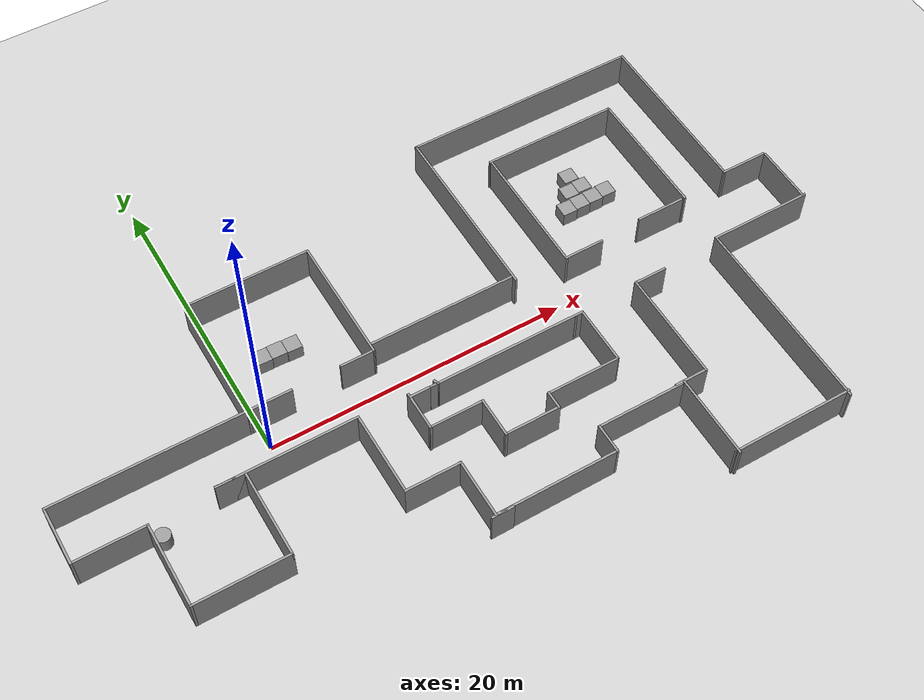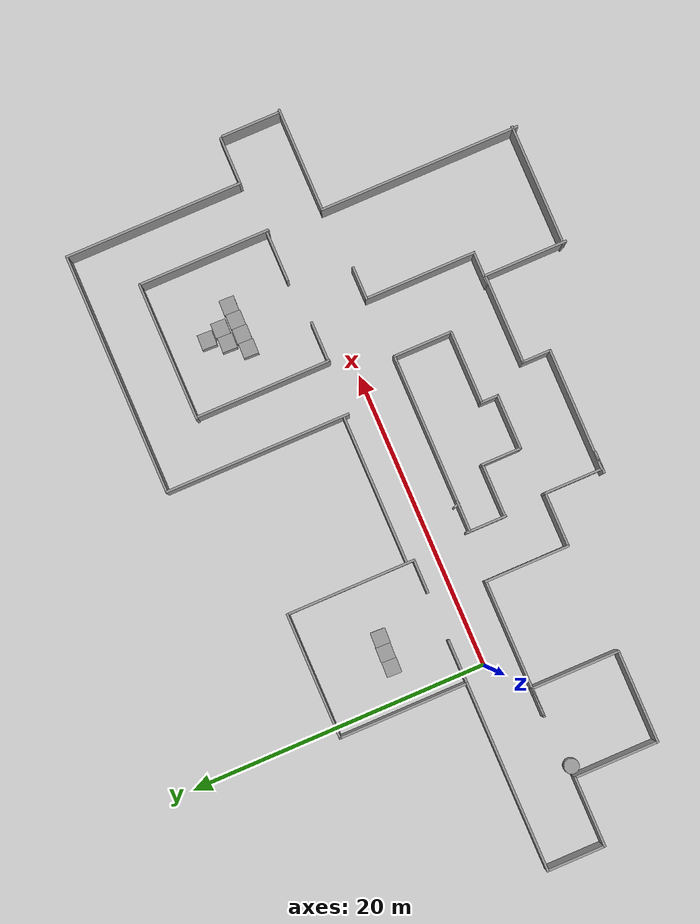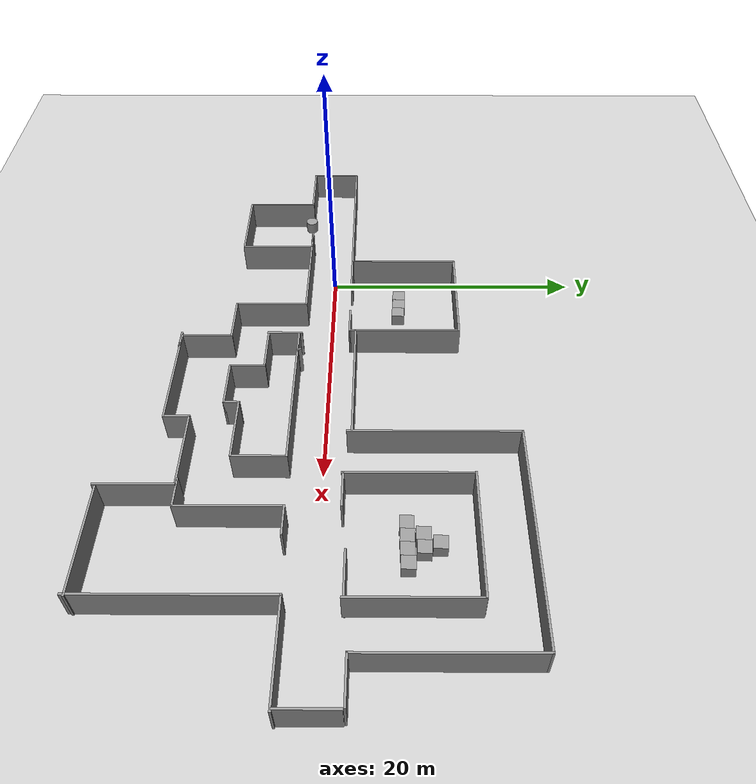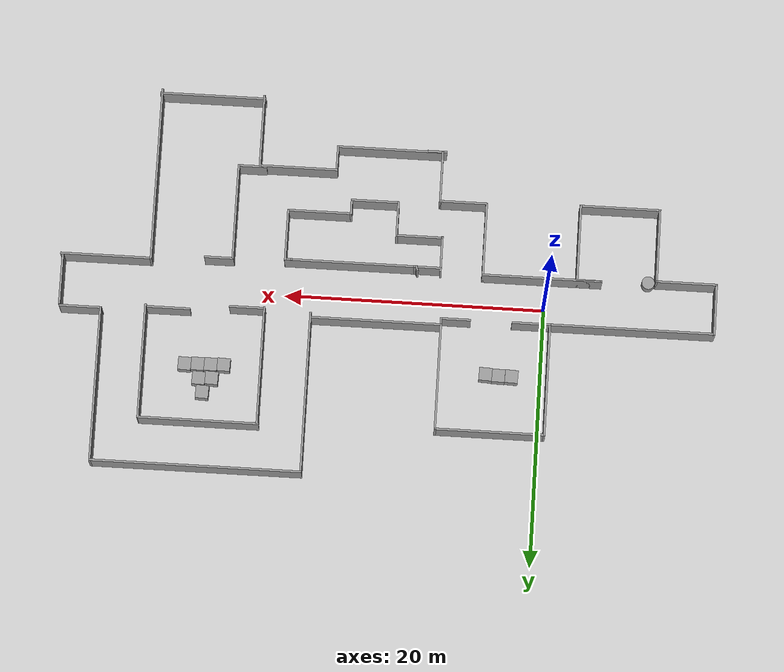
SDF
<sdf version="1.7">
 <world name="default">
  <light name="sun" type="directional">
   <pose>0 0 10 0 -0 0</pose>
   <diffuse>0.8 0.8 0.8 1</diffuse>
   <specular>0.2 0.2 0.2 1</specular>
   <attenuation>
    <range>1000</range>
    <constant>0.9</constant>
    <linear>0.01</linear>
    <quadratic>0.001</quadratic>
   </attenuation>
   <direction>-0.5 0.1 -0.9</direction>
   <spot><inner_angle>0</inner_angle><outer_angle>0</outer_angle><falloff>0</falloff></spot>
  </light>
  <model name="ground_plane">
   <static>1</static>
   <link name="link">
    <collision name="collision">
     <geometry><plane><normal>0 0 1</normal><size>100 100</size></plane></geometry>
     <surface><friction><ode><mu>100</mu><mu2>50</mu2></ode></friction></surface>
    </collision>
    <visual name="visual">
     <cast_shadows>0</cast_shadows>
     <geometry><plane><normal>0 0 1</normal><size>100 100</size></plane></geometry>
     <material>
      <script><uri>file://media/materials/scripts/gazebo.material</uri><name>Gazebo/Grey</name></script>
     </material>
    </visual>
   </link>
  </model>
  <gravity>0 0 -9.8</gravity>
  <magnetic_field>6e-06 2.3e-05 -4.2e-05</magnetic_field>
  <atmosphere type="adiabatic"/>
  <physics type="ode">
   <max_step_size>0.001</max_step_size>
   <real_time_factor>1</real_time_factor>
   <real_time_update_rate>1000</real_time_update_rate>
  </physics>
  <scene><ambient>0.4 0.4 0.4 1</ambient><background>0.7 0.7 0.7 1</background><shadows>1</shadows></scene>
  <spherical_coordinates>
   <surface_model>EARTH_WGS84</surface_model>
   <latitude_deg>0</latitude_deg>
   <longitude_deg>0</longitude_deg>
   <elevation>0</elevation>
   <heading_deg>0</heading_deg>
  </spherical_coordinates>
  <model name="unit_box_clone">
   <pose>2.18485 5.44266 0.499995 0 1e-05 -0.037521</pose>
   <link name="link">
    <inertial>
     <mass>1</mass>
     <inertia>
      <ixx>0.166667</ixx>
      <ixy>0</ixy>
      <ixz>0</ixz>
      <iyy>0.166667</iyy>
      <iyz>0</iyz>
      <izz>0.166667</izz>
     </inertia>
    </inertial>
    <collision name="collision"><geometry><box><size>1 1 1</size></box></geometry></collision>
    <visual name="visual">
     <geometry><box><size>1 1 1</size></box></geometry>
     <material>
      <script><name>Gazebo/Grey</name><uri>file://media/materials/scripts/gazebo.material</uri></script>
     </material>
    </visual>
   </link>
  </model>
  <model name="unit_box_clone_0">
   <pose>3.18635 5.43112 0.499995 1e-05 0 -0.035691</pose>
   <link name="link">
    <inertial>
     <mass>1</mass>
     <inertia>
      <ixx>0.166667</ixx>
      <ixy>0</ixy>
      <ixz>0</ixz>
      <iyy>0.166667</iyy>
      <iyz>0</iyz>
      <izz>0.166667</izz>
     </inertia>
    </inertial>
    <collision name="collision"><geometry><box><size>1 1 1</size></box></geometry></collision>
    <visual name="visual">
     <geometry><box><size>1 1 1</size></box></geometry>
     <material>
      <script><name>Gazebo/Grey</name><uri>file://media/materials/scripts/gazebo.material</uri></script>
     </material>
    </visual>
   </link>
  </model>
  <model name="unit_box_clone_1">
   <pose>4.18492 5.37179 0.499995 1e-05 -0 -0.035732</pose>
   <link name="link">
    <inertial>
     <mass>1</mass>
     <inertia>
      <ixx>0.166667</ixx>
      <ixy>0</ixy>
      <ixz>0</ixz>
      <iyy>0.166667</iyy>
      <iyz>0</iyz>
      <izz>0.166667</izz>
     </inertia>
    </inertial>
    <collision name="collision"><geometry><box><size>1 1 1</size></box></geometry></collision>
    <visual name="visual">
     <geometry><box><size>1 1 1</size></box></geometry>
     <material>
      <script><name>Gazebo/Grey</name><uri>file://media/materials/scripts/gazebo.material</uri></script>
     </material>
    </visual>
   </link>
  </model>
  <model name="unit_box_clone_2">
   <pose>27.3089 5.88323 0.499995 -1e-05 -0 -0.029595</pose>
   <link name="link">
    <inertial>
     <mass>1</mass>
     <inertia>
      <ixx>0.166667</ixx>
      <ixy>0</ixy>
      <ixz>0</ixz>
      <iyy>0.166667</iyy>
      <iyz>0</iyz>
      <izz>0.166667</izz>
     </inertia>
    </inertial>
    <collision name="collision"><geometry><box><size>1 1 1</size></box></geometry></collision>
    <visual name="visual">
     <geometry><box><size>1 1 1</size></box></geometry>
     <material>
      <script><name>Gazebo/Grey</name><uri>file://media/materials/scripts/gazebo.material</uri></script>
     </material>
    </visual>
   </link>
  </model>
  <model name="unit_box_clone_3">
   <pose>26.3071 5.84666 0.499995 -1e-05 -0 -0.029863</pose>
   <link name="link">
    <inertial>
     <mass>1</mass>
     <inertia>
      <ixx>0.166667</ixx>
      <ixy>0</ixy>
      <ixz>0</ixz>
      <iyy>0.166667</iyy>
      <iyz>0</iyz>
      <izz>0.166667</izz>
     </inertia>
    </inertial>
    <collision name="collision"><geometry><box><size>1 1 1</size></box></geometry></collision>
    <visual name="visual">
     <geometry><box><size>1 1 1</size></box></geometry>
     <material>
      <script><name>Gazebo/Grey</name><uri>file://media/materials/scripts/gazebo.material</uri></script>
     </material>
    </visual>
   </link>
  </model>
  <model name="unit_box_clone_4">
   <pose>25.306 5.83514 0.499995 0 -1e-05 -0.02955</pose>
   <link name="link">
    <inertial>
     <mass>1</mass>
     <inertia>
      <ixx>0.166667</ixx>
      <ixy>0</ixy>
      <ixz>0</ixz>
      <iyy>0.166667</iyy>
      <iyz>0</iyz>
      <izz>0.166667</izz>
     </inertia>
    </inertial>
    <collision name="collision"><geometry><box><size>1 1 1</size></box></geometry></collision>
    <visual name="visual">
     <geometry><box><size>1 1 1</size></box></geometry>
     <material>
      <script><name>Gazebo/Grey</name><uri>file://media/materials/scripts/gazebo.material</uri></script>
     </material>
    </visual>
   </link>
  </model>
  <model name="unit_box_clone_5">
   <pose>24.3045 5.81055 0.499995 0 1e-05 -0.029494</pose>
   <link name="link">
    <inertial>
     <mass>1</mass>
     <inertia>
      <ixx>0.166667</ixx>
      <ixy>0</ixy>
      <ixz>0</ixz>
      <iyy>0.166667</iyy>
      <iyz>0</iyz>
      <izz>0.166667</izz>
     </inertia>
    </inertial>
    <collision name="collision"><geometry><box><size>1 1 1</size></box></geometry></collision>
    <visual name="visual">
     <geometry><box><size>1 1 1</size></box></geometry>
     <material>
      <script><name>Gazebo/Grey</name><uri>file://media/materials/scripts/gazebo.material</uri></script>
     </material>
    </visual>
   </link>
  </model>
  <model name="unit_box_clone_6">
   <pose>25.163 6.89754 0.499995 1e-05 -0 -0.0339</pose>
   <link name="link">
    <inertial>
     <mass>1</mass>
     <inertia>
      <ixx>0.166667</ixx>
      <ixy>0</ixy>
      <ixz>0</ixz>
      <iyy>0.166667</iyy>
      <iyz>0</iyz>
      <izz>0.166667</izz>
     </inertia>
    </inertial>
    <collision name="collision"><geometry><box><size>1 1 1</size></box></geometry></collision>
    <visual name="visual">
     <geometry><box><size>1 1 1</size></box></geometry>
     <material>
      <script><name>Gazebo/Grey</name><uri>file://media/materials/scripts/gazebo.material</uri></script>
     </material>
    </visual>
   </link>
  </model>
  <model name="unit_box_clone_7">
   <pose>26.1653 6.94853 0.5 0 -0 -0.0339</pose>
   <link name="link">
    <inertial>
     <mass>1</mass>
     <inertia>
      <ixx>0.166667</ixx>
      <ixy>0</ixy>
      <ixz>0</ixz>
      <iyy>0.166667</iyy>
      <iyz>0</iyz>
      <izz>0.166667</izz>
     </inertia>
    </inertial>
    <collision name="collision"><geometry><box><size>1 1 1</size></box></geometry></collision>
    <visual name="visual">
     <geometry><box><size>1 1 1</size></box></geometry>
     <material>
      <script><name>Gazebo/Grey</name><uri>file://media/materials/scripts/gazebo.material</uri></script>
     </material>
    </visual>
   </link>
  </model>
  <model name="unit_box_clone_8">
   <pose>25.8231 8.01623 0.499995 -1e-05 -0 -0.036844</pose>
   <link name="link">
    <inertial>
     <mass>1</mass>
     <inertia>
      <ixx>0.166667</ixx>
      <ixy>0</ixy>
      <ixz>0</ixz>
      <iyy>0.166667</iyy>
      <iyz>0</iyz>
      <izz>0.166667</izz>
     </inertia>
    </inertial>
    <collision name="collision"><geometry><box><size>1 1 1</size></box></geometry></collision>
    <visual name="visual">
     <geometry><box><size>1 1 1</size></box></geometry>
     <material>
      <script><name>Gazebo/Grey</name><uri>file://media/materials/scripts/gazebo.material</uri></script>
     </material>
    </visual>
   </link>
  </model>
  <model name="unit_cylinder_clone">
   <pose>-7.94709 -2.49222 0.499993 -3e-06 4e-06 5e-06</pose>
   <link name="link">
    <inertial>
     <mass>1</mass>
     <inertia><ixx>0.145833</ixx><ixy>0</ixy><ixz>0</ixz><iyy>0.145833</iyy><iyz>0</iyz><izz>0.125</izz></inertia>
    </inertial>
    <collision name="collision">
     <geometry><cylinder><radius>0.5</radius><length>1</length></cylinder></geometry>
    </collision>
    <visual name="visual">
     <geometry><cylinder><radius>0.5</radius><length>1</length></cylinder></geometry>
     <material>
      <script><name>Gazebo/Grey</name><uri>file://media/materials/scripts/gazebo.material</uri></script>
     </material>
    </visual>
   </link>
  </model>
  <model name="complex_clutter_env03">
   <link name="Wall_0">
    <pose>-25.125 0.163907 0 0 0 -1.5708</pose>
    <visual name="Wall_0_Visual">
     <pose>0 0 1.25 0 -0 0</pose>
     <geometry><box><size>4 0.15 2.5</size></box></geometry>
     <material>
      <script><uri>file://media/materials/scripts/gazebo.material</uri><name>Gazebo/Grey</name></script>
      <ambient>1 1 1 1</ambient>
      <shader type="pixel"/>
     </material>
     <meta><layer>0</layer></meta>
    </visual>
    <collision name="Wall_0_Collision">
     <pose>0 0 1.25 0 -0 0</pose>
     <geometry><box><size>4 0.15 2.5</size></box></geometry>
     <surface>
      <friction>
       <ode><mu>1</mu><mu2>1</mu2><fdir1>0 0 0</fdir1><slip1>0</slip1><slip2>0</slip2></ode>
       <torsional>
        <coefficient>1</coefficient>
        <patch_radius>0</patch_radius>
        <surface_radius>0</surface_radius>
        <use_patch_radius>1</use_patch_radius>
        <ode><slip>0</slip></ode>
       </torsional>
      </friction>
      <bounce><restitution_coefficient>0</restitution_coefficient><threshold>1e+06</threshold></bounce>
      <contact>
       <collide_without_contact>0</collide_without_contact>
       <collide_without_contact_bitmask>1</collide_without_contact_bitmask>
       <collide_bitmask>1</collide_bitmask>
       <ode>
        <soft_cfm>0</soft_cfm>
        <soft_erp>0.2</soft_erp>
        <kp>1e+13</kp>
        <kd>1</kd>
        <max_vel>0.01</max_vel>
        <min_depth>0</min_depth>
       </ode>
       <bullet>
        <split_impulse>1</split_impulse>
        <split_impulse_penetration_threshold>-0.01</split_impulse_penetration_threshold>
        <soft_cfm>0</soft_cfm>
        <soft_erp>0.2</soft_erp>
        <kp>1e+13</kp>
        <kd>1</kd>
       </bullet>
      </contact>
     </surface>
    </collision>
   </link>
   <link name="Wall_1">
    <pose>-22.825 -1.76109 0 0 -0 0</pose>
    <visual name="Wall_1_Visual">
     <pose>0 0 1.25 0 -0 0</pose>
     <geometry><box><size>4.75 0.15 2.5</size></box></geometry>
     <material>
      <script><uri>file://media/materials/scripts/gazebo.material</uri><name>Gazebo/Grey</name></script>
      <ambient>1 1 1 1</ambient>
      <shader type="pixel"/>
     </material>
     <meta><layer>0</layer></meta>
    </visual>
    <collision name="Wall_1_Collision">
     <pose>0 0 1.25 0 -0 0</pose>
     <geometry><box><size>4.75 0.15 2.5</size></box></geometry>
     <surface>
      <friction>
       <ode><mu>1</mu><mu2>1</mu2><fdir1>0 0 0</fdir1><slip1>0</slip1><slip2>0</slip2></ode>
       <torsional>
        <coefficient>1</coefficient>
        <patch_radius>0</patch_radius>
        <surface_radius>0</surface_radius>
        <use_patch_radius>1</use_patch_radius>
        <ode><slip>0</slip></ode>
       </torsional>
      </friction>
      <bounce><restitution_coefficient>0</restitution_coefficient><threshold>1e+06</threshold></bounce>
      <contact>
       <collide_without_contact>0</collide_without_contact>
       <collide_without_contact_bitmask>1</collide_without_contact_bitmask>
       <collide_bitmask>1</collide_bitmask>
       <ode>
        <soft_cfm>0</soft_cfm>
        <soft_erp>0.2</soft_erp>
        <kp>1e+13</kp>
        <kd>1</kd>
        <max_vel>0.01</max_vel>
        <min_depth>0</min_depth>
       </ode>
       <bullet>
        <split_impulse>1</split_impulse>
        <split_impulse_penetration_threshold>-0.01</split_impulse_penetration_threshold>
        <soft_cfm>0</soft_cfm>
        <soft_erp>0.2</soft_erp>
        <kp>1e+13</kp>
        <kd>1</kd>
       </bullet>
      </contact>
     </surface>
    </collision>
   </link>
   <link name="Wall_10">
    <pose>0.474999 -10.9611 0 0 -0 0</pose>
    <visual name="Wall_10_Visual">
     <pose>0 0 1.25 0 -0 0</pose>
     <geometry><box><size>8.25 0.15 2.5</size></box></geometry>
     <material>
      <script><uri>file://media/materials/scripts/gazebo.material</uri><name>Gazebo/Grey</name></script>
      <ambient>1 1 1 1</ambient>
      <shader type="pixel"/>
     </material>
     <meta><layer>0</layer></meta>
    </visual>
    <collision name="Wall_10_Collision">
     <pose>0 0 1.25 0 -0 0</pose>
     <geometry><box><size>8.25 0.15 2.5</size></box></geometry>
     <surface>
      <friction>
       <ode><mu>1</mu><mu2>1</mu2><fdir1>0 0 0</fdir1><slip1>0</slip1><slip2>0</slip2></ode>
       <torsional>
        <coefficient>1</coefficient>
        <patch_radius>0</patch_radius>
        <surface_radius>0</surface_radius>
        <use_patch_radius>1</use_patch_radius>
        <ode><slip>0</slip></ode>
       </torsional>
      </friction>
      <bounce><restitution_coefficient>0</restitution_coefficient><threshold>1e+06</threshold></bounce>
      <contact>
       <collide_without_contact>0</collide_without_contact>
       <collide_without_contact_bitmask>1</collide_without_contact_bitmask>
       <collide_bitmask>1</collide_bitmask>
       <ode>
        <soft_cfm>0</soft_cfm>
        <soft_erp>0.2</soft_erp>
        <kp>1e+13</kp>
        <kd>1</kd>
        <max_vel>0.01</max_vel>
        <min_depth>0</min_depth>
       </ode>
       <bullet>
        <split_impulse>1</split_impulse>
        <split_impulse_penetration_threshold>-0.01</split_impulse_penetration_threshold>
        <soft_cfm>0</soft_cfm>
        <soft_erp>0.2</soft_erp>
        <kp>1e+13</kp>
        <kd>1</kd>
       </bullet>
      </contact>
     </surface>
    </collision>
   </link>
   <link name="Wall_11">
    <pose>4.525 -10.0361 0 0 -0 1.5708</pose>
    <visual name="Wall_11_Visual">
     <pose>0 0 1.25 0 -0 0</pose>
     <geometry><box><size>2 0.15 2.5</size></box></geometry>
     <material>
      <script><uri>file://media/materials/scripts/gazebo.material</uri><name>Gazebo/Grey</name></script>
      <ambient>1 1 1 1</ambient>
      <shader type="pixel"/>
     </material>
     <meta><layer>0</layer></meta>
    </visual>
    <collision name="Wall_11_Collision">
     <pose>0 0 1.25 0 -0 0</pose>
     <geometry><box><size>2 0.15 2.5</size></box></geometry>
     <surface>
      <friction>
       <ode><mu>1</mu><mu2>1</mu2><fdir1>0 0 0</fdir1><slip1>0</slip1><slip2>0</slip2></ode>
       <torsional>
        <coefficient>1</coefficient>
        <patch_radius>0</patch_radius>
        <surface_radius>0</surface_radius>
        <use_patch_radius>1</use_patch_radius>
        <ode><slip>0</slip></ode>
       </torsional>
      </friction>
      <bounce><restitution_coefficient>0</restitution_coefficient><threshold>1e+06</threshold></bounce>
      <contact>
       <collide_without_contact>0</collide_without_contact>
       <collide_without_contact_bitmask>1</collide_without_contact_bitmask>
       <collide_bitmask>1</collide_bitmask>
       <ode>
        <soft_cfm>0</soft_cfm>
        <soft_erp>0.2</soft_erp>
        <kp>1e+13</kp>
        <kd>1</kd>
        <max_vel>0.01</max_vel>
        <min_depth>0</min_depth>
       </ode>
       <bullet>
        <split_impulse>1</split_impulse>
        <split_impulse_penetration_threshold>-0.01</split_impulse_penetration_threshold>
        <soft_cfm>0</soft_cfm>
        <soft_erp>0.2</soft_erp>
        <kp>1e+13</kp>
        <kd>1</kd>
       </bullet>
      </contact>
     </surface>
    </collision>
   </link>
   <link name="Wall_12">
    <pose>7.45 -9.11109 0 0 -0 0</pose>
    <visual name="Wall_12_Visual">
     <pose>0 0 1.25 0 -0 0</pose>
     <geometry><box><size>6 0.15 2.5</size></box></geometry>
     <material>
      <script><uri>file://media/materials/scripts/gazebo.material</uri><name>Gazebo/Grey</name></script>
      <ambient>1 1 1 1</ambient>
      <shader type="pixel"/>
     </material>
     <meta><layer>0</layer></meta>
    </visual>
    <collision name="Wall_12_Collision">
     <pose>0 0 1.25 0 -0 0</pose>
     <geometry><box><size>6 0.15 2.5</size></box></geometry>
     <surface>
      <friction>
       <ode><mu>1</mu><mu2>1</mu2><fdir1>0 0 0</fdir1><slip1>0</slip1><slip2>0</slip2></ode>
       <torsional>
        <coefficient>1</coefficient>
        <patch_radius>0</patch_radius>
        <surface_radius>0</surface_radius>
        <use_patch_radius>1</use_patch_radius>
        <ode><slip>0</slip></ode>
       </torsional>
      </friction>
      <bounce><restitution_coefficient>0</restitution_coefficient><threshold>1e+06</threshold></bounce>
      <contact>
       <collide_without_contact>0</collide_without_contact>
       <collide_without_contact_bitmask>1</collide_without_contact_bitmask>
       <collide_bitmask>1</collide_bitmask>
       <ode>
        <soft_cfm>0</soft_cfm>
        <soft_erp>0.2</soft_erp>
        <kp>1e+13</kp>
        <kd>1</kd>
        <max_vel>0.01</max_vel>
        <min_depth>0</min_depth>
       </ode>
       <bullet>
        <split_impulse>1</split_impulse>
        <split_impulse_penetration_threshold>-0.01</split_impulse_penetration_threshold>
        <soft_cfm>0</soft_cfm>
        <soft_erp>0.2</soft_erp>
        <kp>1e+13</kp>
        <kd>1</kd>
       </bullet>
      </contact>
     </surface>
    </collision>
   </link>
   <link name="Wall_17">
    <pose>5.64389 -5.72165 0 0 -0 3.14159</pose>
    <inertial>
     <inertia><ixx>0</ixx><ixy>0</ixy><ixz>0</ixz><iyy>0</iyy><iyz>0</iyz><izz>0</izz></inertia>
     <mass>0</mass>
    </inertial>
    <visual name="Wall_17_Visual">
     <pose>0 0 1.25 0 -0 0</pose>
     <geometry><box><size>4.80321 0.15 2.5</size></box></geometry>
     <material>
      <script><uri>file://media/materials/scripts/gazebo.material</uri><name>Gazebo/Grey</name></script>
      <ambient>1 1 1 1</ambient>
      <shader type="pixel"/>
     </material>
     <meta><layer>0</layer></meta>
    </visual>
    <collision name="Wall_17_Collision">
     <pose>0 0 1.25 0 -0 0</pose>
     <geometry><box><size>4.80321 0.15 2.5</size></box></geometry>
     <surface>
      <friction>
       <ode><mu>1</mu><mu2>1</mu2><fdir1>0 0 0</fdir1><slip1>0</slip1><slip2>0</slip2></ode>
       <torsional>
        <coefficient>1</coefficient>
        <patch_radius>0</patch_radius>
        <surface_radius>0</surface_radius>
        <use_patch_radius>1</use_patch_radius>
        <ode><slip>0</slip></ode>
       </torsional>
      </friction>
      <bounce><restitution_coefficient>0</restitution_coefficient><threshold>1e+06</threshold></bounce>
      <contact>
       <collide_without_contact>0</collide_without_contact>
       <collide_without_contact_bitmask>1</collide_without_contact_bitmask>
       <collide_bitmask>1</collide_bitmask>
       <ode>
        <soft_cfm>0</soft_cfm>
        <soft_erp>0.2</soft_erp>
        <kp>1e+13</kp>
        <kd>1</kd>
        <max_vel>0.01</max_vel>
        <min_depth>0</min_depth>
       </ode>
       <bullet>
        <split_impulse>1</split_impulse>
        <split_impulse_penetration_threshold>-0.01</split_impulse_penetration_threshold>
        <soft_cfm>0</soft_cfm>
        <soft_erp>0.2</soft_erp>
        <kp>1e+13</kp>
        <kd>1</kd>
       </bullet>
      </contact>
     </surface>
    </collision>
   </link>
   <link name="Wall_18">
    <pose>3.21498 -6.25822 0 0 0 -1.5708</pose>
    <visual name="Wall_18_Visual">
     <pose>0 0 1.25 0 -0 0</pose>
     <geometry><box><size>1.25 0.15 2.5</size></box></geometry>
     <material>
      <script><uri>file://media/materials/scripts/gazebo.material</uri><name>Gazebo/Grey</name></script>
      <ambient>1 1 1 1</ambient>
      <shader type="pixel"/>
     </material>
     <meta><layer>0</layer></meta>
    </visual>
    <collision name="Wall_18_Collision">
     <pose>0 0 1.25 0 -0 0</pose>
     <geometry><box><size>1.25 0.15 2.5</size></box></geometry>
     <surface>
      <friction>
       <ode><mu>1</mu><mu2>1</mu2><fdir1>0 0 0</fdir1><slip1>0</slip1><slip2>0</slip2></ode>
       <torsional>
        <coefficient>1</coefficient>
        <patch_radius>0</patch_radius>
        <surface_radius>0</surface_radius>
        <use_patch_radius>1</use_patch_radius>
        <ode><slip>0</slip></ode>
       </torsional>
      </friction>
      <bounce><restitution_coefficient>0</restitution_coefficient><threshold>1e+06</threshold></bounce>
      <contact>
       <collide_without_contact>0</collide_without_contact>
       <collide_without_contact_bitmask>1</collide_without_contact_bitmask>
       <collide_bitmask>1</collide_bitmask>
       <ode>
        <soft_cfm>0</soft_cfm>
        <soft_erp>0.2</soft_erp>
        <kp>1e+13</kp>
        <kd>1</kd>
        <max_vel>0.01</max_vel>
        <min_depth>0</min_depth>
       </ode>
       <bullet>
        <split_impulse>1</split_impulse>
        <split_impulse_penetration_threshold>-0.01</split_impulse_penetration_threshold>
        <soft_cfm>0</soft_cfm>
        <soft_erp>0.2</soft_erp>
        <kp>1e+13</kp>
        <kd>1</kd>
       </bullet>
      </contact>
     </surface>
    </collision>
   </link>
   <link name="Wall_19">
    <pose>1.41498 -6.80822 0 0 -0 3.14159</pose>
    <visual name="Wall_19_Visual">
     <pose>0 0 1.25 0 -0 0</pose>
     <geometry><box><size>3.75 0.15 2.5</size></box></geometry>
     <material>
      <script><uri>file://media/materials/scripts/gazebo.material</uri><name>Gazebo/Grey</name></script>
      <ambient>1 1 1 1</ambient>
      <shader type="pixel"/>
     </material>
     <meta><layer>0</layer></meta>
    </visual>
    <collision name="Wall_19_Collision">
     <pose>0 0 1.25 0 -0 0</pose>
     <geometry><box><size>3.75 0.15 2.5</size></box></geometry>
     <surface>
      <friction>
       <ode><mu>1</mu><mu2>1</mu2><fdir1>0 0 0</fdir1><slip1>0</slip1><slip2>0</slip2></ode>
       <torsional>
        <coefficient>1</coefficient>
        <patch_radius>0</patch_radius>
        <surface_radius>0</surface_radius>
        <use_patch_radius>1</use_patch_radius>
        <ode><slip>0</slip></ode>
       </torsional>
      </friction>
      <bounce><restitution_coefficient>0</restitution_coefficient><threshold>1e+06</threshold></bounce>
      <contact>
       <collide_without_contact>0</collide_without_contact>
       <collide_without_contact_bitmask>1</collide_without_contact_bitmask>
       <collide_bitmask>1</collide_bitmask>
       <ode>
        <soft_cfm>0</soft_cfm>
        <soft_erp>0.2</soft_erp>
        <kp>1e+13</kp>
        <kd>1</kd>
        <max_vel>0.01</max_vel>
        <min_depth>0</min_depth>
       </ode>
       <bullet>
        <split_impulse>1</split_impulse>
        <split_impulse_penetration_threshold>-0.01</split_impulse_penetration_threshold>
        <soft_cfm>0</soft_cfm>
        <soft_erp>0.2</soft_erp>
        <kp>1e+13</kp>
        <kd>1</kd>
       </bullet>
      </contact>
     </surface>
    </collision>
   </link>
   <link name="Wall_2">
    <pose>-20.525 -4.56109 0 0 0 -1.5708</pose>
    <visual name="Wall_2_Visual">
     <pose>0 0 1.25 0 -0 0</pose>
     <geometry><box><size>5.75 0.15 2.5</size></box></geometry>
     <material>
      <script><uri>file://media/materials/scripts/gazebo.material</uri><name>Gazebo/Grey</name></script>
      <ambient>1 1 1 1</ambient>
      <shader type="pixel"/>
     </material>
     <meta><layer>0</layer></meta>
    </visual>
    <collision name="Wall_2_Collision">
     <pose>0 0 1.25 0 -0 0</pose>
     <geometry><box><size>5.75 0.15 2.5</size></box></geometry>
     <surface>
      <friction>
       <ode><mu>1</mu><mu2>1</mu2><fdir1>0 0 0</fdir1><slip1>0</slip1><slip2>0</slip2></ode>
       <torsional>
        <coefficient>1</coefficient>
        <patch_radius>0</patch_radius>
        <surface_radius>0</surface_radius>
        <use_patch_radius>1</use_patch_radius>
        <ode><slip>0</slip></ode>
       </torsional>
      </friction>
      <bounce><restitution_coefficient>0</restitution_coefficient><threshold>1e+06</threshold></bounce>
      <contact>
       <collide_without_contact>0</collide_without_contact>
       <collide_without_contact_bitmask>1</collide_without_contact_bitmask>
       <collide_bitmask>1</collide_bitmask>
       <ode>
        <soft_cfm>0</soft_cfm>
        <soft_erp>0.2</soft_erp>
        <kp>1e+13</kp>
        <kd>1</kd>
        <max_vel>0.01</max_vel>
        <min_depth>0</min_depth>
       </ode>
       <bullet>
        <split_impulse>1</split_impulse>
        <split_impulse_penetration_threshold>-0.01</split_impulse_penetration_threshold>
        <soft_cfm>0</soft_cfm>
        <soft_erp>0.2</soft_erp>
        <kp>1e+13</kp>
        <kd>1</kd>
       </bullet>
      </contact>
     </surface>
    </collision>
   </link>
   <link name="Wall_20">
    <pose>-0.38502 -5.50822 0 0 -0 1.5708</pose>
    <visual name="Wall_20_Visual">
     <pose>0 0 1.25 0 -0 0</pose>
     <geometry><box><size>2.75 0.15 2.5</size></box></geometry>
     <material>
      <script><uri>file://media/materials/scripts/gazebo.material</uri><name>Gazebo/Grey</name></script>
      <ambient>1 1 1 1</ambient>
      <shader type="pixel"/>
     </material>
     <meta><layer>0</layer></meta>
    </visual>
    <collision name="Wall_20_Collision">
     <pose>0 0 1.25 0 -0 0</pose>
     <geometry><box><size>2.75 0.15 2.5</size></box></geometry>
     <surface>
      <friction>
       <ode><mu>1</mu><mu2>1</mu2><fdir1>0 0 0</fdir1><slip1>0</slip1><slip2>0</slip2></ode>
       <torsional>
        <coefficient>1</coefficient>
        <patch_radius>0</patch_radius>
        <surface_radius>0</surface_radius>
        <use_patch_radius>1</use_patch_radius>
        <ode><slip>0</slip></ode>
       </torsional>
      </friction>
      <bounce><restitution_coefficient>0</restitution_coefficient><threshold>1e+06</threshold></bounce>
      <contact>
       <collide_without_contact>0</collide_without_contact>
       <collide_without_contact_bitmask>1</collide_without_contact_bitmask>
       <collide_bitmask>1</collide_bitmask>
       <ode>
        <soft_cfm>0</soft_cfm>
        <soft_erp>0.2</soft_erp>
        <kp>1e+13</kp>
        <kd>1</kd>
        <max_vel>0.01</max_vel>
        <min_depth>0</min_depth>
       </ode>
       <bullet>
        <split_impulse>1</split_impulse>
        <split_impulse_penetration_threshold>-0.01</split_impulse_penetration_threshold>
        <soft_cfm>0</soft_cfm>
        <soft_erp>0.2</soft_erp>
        <kp>1e+13</kp>
        <kd>1</kd>
       </bullet>
      </contact>
     </surface>
    </collision>
   </link>
   <link name="Wall_21">
    <pose>-2.21136 -4.22012 0 0 -0 3.14159</pose>
    <inertial>
     <inertia><ixx>0</ixx><ixy>0</ixy><ixz>0</ixz><iyy>0</iyy><iyz>0</iyz><izz>0</izz></inertia>
     <mass>0</mass>
    </inertial>
    <visual name="Wall_21_Visual">
     <pose>0 0 1.25 0 -0 0</pose>
     <geometry><box><size>3.55406 0.15 2.5</size></box></geometry>
     <material>
      <script><uri>file://media/materials/scripts/gazebo.material</uri><name>Gazebo/Grey</name></script>
      <ambient>1 1 1 1</ambient>
      <shader type="pixel"/>
     </material>
     <meta><layer>0</layer></meta>
    </visual>
    <collision name="Wall_21_Collision">
     <pose>0 0 1.25 0 -0 0</pose>
     <geometry><box><size>3.55406 0.15 2.5</size></box></geometry>
     <surface>
      <friction>
       <ode><mu>1</mu><mu2>1</mu2><fdir1>0 0 0</fdir1><slip1>0</slip1><slip2>0</slip2></ode>
       <torsional>
        <coefficient>1</coefficient>
        <patch_radius>0</patch_radius>
        <surface_radius>0</surface_radius>
        <use_patch_radius>1</use_patch_radius>
        <ode><slip>0</slip></ode>
       </torsional>
      </friction>
      <bounce><restitution_coefficient>0</restitution_coefficient><threshold>1e+06</threshold></bounce>
      <contact>
       <collide_without_contact>0</collide_without_contact>
       <collide_without_contact_bitmask>1</collide_without_contact_bitmask>
       <collide_bitmask>1</collide_bitmask>
       <ode>
        <soft_cfm>0</soft_cfm>
        <soft_erp>0.2</soft_erp>
        <kp>1e+13</kp>
        <kd>1</kd>
        <max_vel>0.01</max_vel>
        <min_depth>0</min_depth>
       </ode>
       <bullet>
        <split_impulse>1</split_impulse>
        <split_impulse_penetration_threshold>-0.01</split_impulse_penetration_threshold>
        <soft_cfm>0</soft_cfm>
        <soft_erp>0.2</soft_erp>
        <kp>1e+13</kp>
        <kd>1</kd>
       </bullet>
      </contact>
     </surface>
    </collision>
   </link>
   <link name="Wall_22">
    <pose>-3.91022 -2.95498 0 0 -0 1.5708</pose>
    <visual name="Wall_22_Visual">
     <pose>0 0 1.25 0 -0 0</pose>
     <geometry><box><size>2.75 0.15 2.5</size></box></geometry>
     <material>
      <script><uri>file://media/materials/scripts/gazebo.material</uri><name>Gazebo/Grey</name></script>
      <ambient>1 1 1 1</ambient>
      <shader type="pixel"/>
     </material>
     <meta><layer>0</layer></meta>
    </visual>
    <collision name="Wall_22_Collision">
     <pose>0 0 1.25 0 -0 0</pose>
     <geometry><box><size>2.75 0.15 2.5</size></box></geometry>
     <surface>
      <friction>
       <ode><mu>1</mu><mu2>1</mu2><fdir1>0 0 0</fdir1><slip1>0</slip1><slip2>0</slip2></ode>
       <torsional>
        <coefficient>1</coefficient>
        <patch_radius>0</patch_radius>
        <surface_radius>0</surface_radius>
        <use_patch_radius>1</use_patch_radius>
        <ode><slip>0</slip></ode>
       </torsional>
      </friction>
      <bounce><restitution_coefficient>0</restitution_coefficient><threshold>1e+06</threshold></bounce>
      <contact>
       <collide_without_contact>0</collide_without_contact>
       <collide_without_contact_bitmask>1</collide_without_contact_bitmask>
       <collide_bitmask>1</collide_bitmask>
       <ode>
        <soft_cfm>0</soft_cfm>
        <soft_erp>0.2</soft_erp>
        <kp>1e+13</kp>
        <kd>1</kd>
        <max_vel>0.01</max_vel>
        <min_depth>0</min_depth>
       </ode>
       <bullet>
        <split_impulse>1</split_impulse>
        <split_impulse_penetration_threshold>-0.01</split_impulse_penetration_threshold>
        <soft_cfm>0</soft_cfm>
        <soft_erp>0.2</soft_erp>
        <kp>1e+13</kp>
        <kd>1</kd>
       </bullet>
      </contact>
     </surface>
    </collision>
   </link>
   <link name="Wall_25">
    <pose>8.05058 -3.7763 0 0 -0 1.5708</pose>
    <visual name="Wall_25_Visual">
     <pose>0 0 1.25 0 -0 0</pose>
     <geometry><box><size>4 0.15 2.5</size></box></geometry>
     <material>
      <script><uri>file://media/materials/scripts/gazebo.material</uri><name>Gazebo/Grey</name></script>
      <ambient>1 1 1 1</ambient>
      <shader type="pixel"/>
     </material>
     <meta><layer>0</layer></meta>
    </visual>
    <collision name="Wall_25_Collision">
     <pose>0 0 1.25 0 -0 0</pose>
     <geometry><box><size>4 0.15 2.5</size></box></geometry>
     <surface>
      <friction>
       <ode><mu>1</mu><mu2>1</mu2><fdir1>0 0 0</fdir1><slip1>0</slip1><slip2>0</slip2></ode>
       <torsional>
        <coefficient>1</coefficient>
        <patch_radius>0</patch_radius>
        <surface_radius>0</surface_radius>
        <use_patch_radius>1</use_patch_radius>
        <ode><slip>0</slip></ode>
       </torsional>
      </friction>
      <bounce><restitution_coefficient>0</restitution_coefficient><threshold>1e+06</threshold></bounce>
      <contact>
       <collide_without_contact>0</collide_without_contact>
       <collide_without_contact_bitmask>1</collide_without_contact_bitmask>
       <collide_bitmask>1</collide_bitmask>
       <ode>
        <soft_cfm>0</soft_cfm>
        <soft_erp>0.2</soft_erp>
        <kp>1e+13</kp>
        <kd>1</kd>
        <max_vel>0.01</max_vel>
        <min_depth>0</min_depth>
       </ode>
       <bullet>
        <split_impulse>1</split_impulse>
        <split_impulse_penetration_threshold>-0.01</split_impulse_penetration_threshold>
        <soft_cfm>0</soft_cfm>
        <soft_erp>0.2</soft_erp>
        <kp>1e+13</kp>
        <kd>1</kd>
       </bullet>
      </contact>
     </surface>
    </collision>
   </link>
   <link name="Wall_26">
    <pose>7.56498 -1.85822 0 0 -0 0</pose>
    <visual name="Wall_26_Visual">
     <pose>0 0 1.25 0 -0 0</pose>
     <geometry><box><size>0.15 0.15 2.5</size></box></geometry>
     <material>
      <script><uri>file://media/materials/scripts/gazebo.material</uri><name>Gazebo/Grey</name></script>
      <ambient>1 1 1 1</ambient>
      <shader type="pixel"/>
     </material>
     <meta><layer>0</layer></meta>
    </visual>
    <collision name="Wall_26_Collision">
     <pose>0 0 1.25 0 -0 0</pose>
     <geometry><box><size>0.15 0.15 2.5</size></box></geometry>
     <surface>
      <friction>
       <ode><mu>1</mu><mu2>1</mu2><fdir1>0 0 0</fdir1><slip1>0</slip1><slip2>0</slip2></ode>
       <torsional>
        <coefficient>1</coefficient>
        <patch_radius>0</patch_radius>
        <surface_radius>0</surface_radius>
        <use_patch_radius>1</use_patch_radius>
        <ode><slip>0</slip></ode>
       </torsional>
      </friction>
      <bounce><restitution_coefficient>0</restitution_coefficient><threshold>1e+06</threshold></bounce>
      <contact>
       <collide_without_contact>0</collide_without_contact>
       <collide_without_contact_bitmask>1</collide_without_contact_bitmask>
       <collide_bitmask>1</collide_bitmask>
       <ode>
        <soft_cfm>0</soft_cfm>
        <soft_erp>0.2</soft_erp>
        <kp>1e+13</kp>
        <kd>1</kd>
        <max_vel>0.01</max_vel>
        <min_depth>0</min_depth>
       </ode>
       <bullet>
        <split_impulse>1</split_impulse>
        <split_impulse_penetration_threshold>-0.01</split_impulse_penetration_threshold>
        <soft_cfm>0</soft_cfm>
        <soft_erp>0.2</soft_erp>
        <kp>1e+13</kp>
        <kd>1</kd>
       </bullet>
      </contact>
     </surface>
    </collision>
   </link>
   <link name="Wall_28">
    <pose>-18.825 2.08891 0 0 -0 0</pose>
    <visual name="Wall_28_Visual">
     <pose>0 0 1.25 0 -0 0</pose>
     <geometry><box><size>12.75 0.15 2.5</size></box></geometry>
     <material>
      <script><uri>file://media/materials/scripts/gazebo.material</uri><name>Gazebo/Grey</name></script>
      <ambient>1 1 1 1</ambient>
      <shader type="pixel"/>
     </material>
     <meta><layer>0</layer></meta>
    </visual>
    <collision name="Wall_28_Collision">
     <pose>0 0 1.25 0 -0 0</pose>
     <geometry><box><size>12.75 0.15 2.5</size></box></geometry>
     <surface>
      <friction>
       <ode><mu>1</mu><mu2>1</mu2><fdir1>0 0 0</fdir1><slip1>0</slip1><slip2>0</slip2></ode>
       <torsional>
        <coefficient>1</coefficient>
        <patch_radius>0</patch_radius>
        <surface_radius>0</surface_radius>
        <use_patch_radius>1</use_patch_radius>
        <ode><slip>0</slip></ode>
       </torsional>
      </friction>
      <bounce><restitution_coefficient>0</restitution_coefficient><threshold>1e+06</threshold></bounce>
      <contact>
       <collide_without_contact>0</collide_without_contact>
       <collide_without_contact_bitmask>1</collide_without_contact_bitmask>
       <collide_bitmask>1</collide_bitmask>
       <ode>
        <soft_cfm>0</soft_cfm>
        <soft_erp>0.2</soft_erp>
        <kp>1e+13</kp>
        <kd>1</kd>
        <max_vel>0.01</max_vel>
        <min_depth>0</min_depth>
       </ode>
       <bullet>
        <split_impulse>1</split_impulse>
        <split_impulse_penetration_threshold>-0.01</split_impulse_penetration_threshold>
        <soft_cfm>0</soft_cfm>
        <soft_erp>0.2</soft_erp>
        <kp>1e+13</kp>
        <kd>1</kd>
       </bullet>
      </contact>
     </surface>
    </collision>
   </link>
   <link name="Wall_29">
    <pose>-12.525 6.38891 0 0 -0 1.5708</pose>
    <visual name="Wall_29_Visual">
     <pose>0 0 1.25 0 -0 0</pose>
     <geometry><box><size>8.75 0.15 2.5</size></box></geometry>
     <material>
      <script><uri>file://media/materials/scripts/gazebo.material</uri><name>Gazebo/Grey</name></script>
      <ambient>1 1 1 1</ambient>
      <shader type="pixel"/>
     </material>
     <meta><layer>0</layer></meta>
    </visual>
    <collision name="Wall_29_Collision">
     <pose>0 0 1.25 0 -0 0</pose>
     <geometry><box><size>8.75 0.15 2.5</size></box></geometry>
     <surface>
      <friction>
       <ode><mu>1</mu><mu2>1</mu2><fdir1>0 0 0</fdir1><slip1>0</slip1><slip2>0</slip2></ode>
       <torsional>
        <coefficient>1</coefficient>
        <patch_radius>0</patch_radius>
        <surface_radius>0</surface_radius>
        <use_patch_radius>1</use_patch_radius>
        <ode><slip>0</slip></ode>
       </torsional>
      </friction>
      <bounce><restitution_coefficient>0</restitution_coefficient><threshold>1e+06</threshold></bounce>
      <contact>
       <collide_without_contact>0</collide_without_contact>
       <collide_without_contact_bitmask>1</collide_without_contact_bitmask>
       <collide_bitmask>1</collide_bitmask>
       <ode>
        <soft_cfm>0</soft_cfm>
        <soft_erp>0.2</soft_erp>
        <kp>1e+13</kp>
        <kd>1</kd>
        <max_vel>0.01</max_vel>
        <min_depth>0</min_depth>
       </ode>
       <bullet>
        <split_impulse>1</split_impulse>
        <split_impulse_penetration_threshold>-0.01</split_impulse_penetration_threshold>
        <soft_cfm>0</soft_cfm>
        <soft_erp>0.2</soft_erp>
        <kp>1e+13</kp>
        <kd>1</kd>
       </bullet>
      </contact>
     </surface>
    </collision>
   </link>
   <link name="Wall_3">
    <pose>-17.475 -7.36109 0 0 -0 0</pose>
    <visual name="Wall_3_Visual">
     <pose>0 0 1.25 0 -0 0</pose>
     <geometry><box><size>6.25 0.15 2.5</size></box></geometry>
     <material>
      <script><uri>file://media/materials/scripts/gazebo.material</uri><name>Gazebo/Grey</name></script>
      <ambient>1 1 1 1</ambient>
      <shader type="pixel"/>
     </material>
     <meta><layer>0</layer></meta>
    </visual>
    <collision name="Wall_3_Collision">
     <pose>0 0 1.25 0 -0 0</pose>
     <geometry><box><size>6.25 0.15 2.5</size></box></geometry>
     <surface>
      <friction>
       <ode><mu>1</mu><mu2>1</mu2><fdir1>0 0 0</fdir1><slip1>0</slip1><slip2>0</slip2></ode>
       <torsional>
        <coefficient>1</coefficient>
        <patch_radius>0</patch_radius>
        <surface_radius>0</surface_radius>
        <use_patch_radius>1</use_patch_radius>
        <ode><slip>0</slip></ode>
       </torsional>
      </friction>
      <bounce><restitution_coefficient>0</restitution_coefficient><threshold>1e+06</threshold></bounce>
      <contact>
       <collide_without_contact>0</collide_without_contact>
       <collide_without_contact_bitmask>1</collide_without_contact_bitmask>
       <collide_bitmask>1</collide_bitmask>
       <ode>
        <soft_cfm>0</soft_cfm>
        <soft_erp>0.2</soft_erp>
        <kp>1e+13</kp>
        <kd>1</kd>
        <max_vel>0.01</max_vel>
        <min_depth>0</min_depth>
       </ode>
       <bullet>
        <split_impulse>1</split_impulse>
        <split_impulse_penetration_threshold>-0.01</split_impulse_penetration_threshold>
        <soft_cfm>0</soft_cfm>
        <soft_erp>0.2</soft_erp>
        <kp>1e+13</kp>
        <kd>1</kd>
       </bullet>
      </contact>
     </surface>
    </collision>
   </link>
   <link name="Wall_30">
    <pose>-8.35 10.6889 0 0 -0 0</pose>
    <visual name="Wall_30_Visual">
     <pose>0 0 1.25 0 -0 0</pose>
     <geometry><box><size>8.5 0.15 2.5</size></box></geometry>
     <material>
      <script><uri>file://media/materials/scripts/gazebo.material</uri><name>Gazebo/Grey</name></script>
      <ambient>1 1 1 1</ambient>
      <shader type="pixel"/>
     </material>
     <meta><layer>0</layer></meta>
    </visual>
    <collision name="Wall_30_Collision">
     <pose>0 0 1.25 0 -0 0</pose>
     <geometry><box><size>8.5 0.15 2.5</size></box></geometry>
     <surface>
      <friction>
       <ode><mu>1</mu><mu2>1</mu2><fdir1>0 0 0</fdir1><slip1>0</slip1><slip2>0</slip2></ode>
       <torsional>
        <coefficient>1</coefficient>
        <patch_radius>0</patch_radius>
        <surface_radius>0</surface_radius>
        <use_patch_radius>1</use_patch_radius>
        <ode><slip>0</slip></ode>
       </torsional>
      </friction>
      <bounce><restitution_coefficient>0</restitution_coefficient><threshold>1e+06</threshold></bounce>
      <contact>
       <collide_without_contact>0</collide_without_contact>
       <collide_without_contact_bitmask>1</collide_without_contact_bitmask>
       <collide_bitmask>1</collide_bitmask>
       <ode>
        <soft_cfm>0</soft_cfm>
        <soft_erp>0.2</soft_erp>
        <kp>1e+13</kp>
        <kd>1</kd>
        <max_vel>0.01</max_vel>
        <min_depth>0</min_depth>
       </ode>
       <bullet>
        <split_impulse>1</split_impulse>
        <split_impulse_penetration_threshold>-0.01</split_impulse_penetration_threshold>
        <soft_cfm>0</soft_cfm>
        <soft_erp>0.2</soft_erp>
        <kp>1e+13</kp>
        <kd>1</kd>
       </bullet>
      </contact>
     </surface>
    </collision>
   </link>
   <link name="Wall_31">
    <pose>-4.175 6.38891 0 0 0 -1.5708</pose>
    <visual name="Wall_31_Visual">
     <pose>0 0 1.25 0 -0 0</pose>
     <geometry><box><size>8.75 0.15 2.5</size></box></geometry>
     <material>
      <script><uri>file://media/materials/scripts/gazebo.material</uri><name>Gazebo/Grey</name></script>
      <ambient>1 1 1 1</ambient>
      <shader type="pixel"/>
     </material>
     <meta><layer>0</layer></meta>
    </visual>
    <collision name="Wall_31_Collision">
     <pose>0 0 1.25 0 -0 0</pose>
     <geometry><box><size>8.75 0.15 2.5</size></box></geometry>
     <surface>
      <friction>
       <ode><mu>1</mu><mu2>1</mu2><fdir1>0 0 0</fdir1><slip1>0</slip1><slip2>0</slip2></ode>
       <torsional>
        <coefficient>1</coefficient>
        <patch_radius>0</patch_radius>
        <surface_radius>0</surface_radius>
        <use_patch_radius>1</use_patch_radius>
        <ode><slip>0</slip></ode>
       </torsional>
      </friction>
      <bounce><restitution_coefficient>0</restitution_coefficient><threshold>1e+06</threshold></bounce>
      <contact>
       <collide_without_contact>0</collide_without_contact>
       <collide_without_contact_bitmask>1</collide_without_contact_bitmask>
       <collide_bitmask>1</collide_bitmask>
       <ode>
        <soft_cfm>0</soft_cfm>
        <soft_erp>0.2</soft_erp>
        <kp>1e+13</kp>
        <kd>1</kd>
        <max_vel>0.01</max_vel>
        <min_depth>0</min_depth>
       </ode>
       <bullet>
        <split_impulse>1</split_impulse>
        <split_impulse_penetration_threshold>-0.01</split_impulse_penetration_threshold>
        <soft_cfm>0</soft_cfm>
        <soft_erp>0.2</soft_erp>
        <kp>1e+13</kp>
        <kd>1</kd>
       </bullet>
      </contact>
     </surface>
    </collision>
   </link>
   <link name="Wall_33">
    <pose>9.40943 6.5233 0 0 -0 1.5708</pose>
    <inertial>
     <inertia><ixx>0</ixx><ixy>0</ixy><ixz>0</ixz><iyy>0</iyy><iyz>0</iyz><izz>0</izz></inertia>
     <mass>0</mass>
    </inertial>
    <visual name="Wall_33_Visual">
     <pose>0 0 1.25 0 -0 0</pose>
     <geometry><box><size>9.11585 0.15 2.5</size></box></geometry>
     <material>
      <script><uri>file://media/materials/scripts/gazebo.material</uri><name>Gazebo/Grey</name></script>
      <ambient>1 1 1 1</ambient>
      <shader type="pixel"/>
     </material>
     <meta><layer>0</layer></meta>
    </visual>
    <collision name="Wall_33_Collision">
     <pose>0 0 1.25 0 -0 0</pose>
     <geometry><box><size>9.11585 0.15 2.5</size></box></geometry>
     <surface>
      <friction>
       <ode><mu>1</mu><mu2>1</mu2><fdir1>0 0 0</fdir1><slip1>0</slip1><slip2>0</slip2></ode>
       <torsional>
        <coefficient>1</coefficient>
        <patch_radius>0</patch_radius>
        <surface_radius>0</surface_radius>
        <use_patch_radius>1</use_patch_radius>
        <ode><slip>0</slip></ode>
       </torsional>
      </friction>
      <bounce><restitution_coefficient>0</restitution_coefficient><threshold>1e+06</threshold></bounce>
      <contact>
       <collide_without_contact>0</collide_without_contact>
       <collide_without_contact_bitmask>1</collide_without_contact_bitmask>
       <collide_bitmask>1</collide_bitmask>
       <ode>
        <soft_cfm>0</soft_cfm>
        <soft_erp>0.2</soft_erp>
        <kp>1e+13</kp>
        <kd>1</kd>
        <max_vel>0.01</max_vel>
        <min_depth>0</min_depth>
       </ode>
       <bullet>
        <split_impulse>1</split_impulse>
        <split_impulse_penetration_threshold>-0.01</split_impulse_penetration_threshold>
        <soft_cfm>0</soft_cfm>
        <soft_erp>0.2</soft_erp>
        <kp>1e+13</kp>
        <kd>1</kd>
       </bullet>
      </contact>
     </surface>
    </collision>
   </link>
   <link name="Wall_34">
    <pose>13.9057 11.0918 0 0 -0 0</pose>
    <visual name="Wall_34_Visual">
     <pose>0 0 1.25 0 -0 0</pose>
     <geometry><box><size>9.25 0.15 2.5</size></box></geometry>
     <material>
      <script><uri>file://media/materials/scripts/gazebo.material</uri><name>Gazebo/Grey</name></script>
      <ambient>1 1 1 1</ambient>
      <shader type="pixel"/>
     </material>
     <meta><layer>0</layer></meta>
    </visual>
    <collision name="Wall_34_Collision">
     <pose>0 0 1.25 0 -0 0</pose>
     <geometry><box><size>9.25 0.15 2.5</size></box></geometry>
     <surface>
      <friction>
       <ode><mu>1</mu><mu2>1</mu2><fdir1>0 0 0</fdir1><slip1>0</slip1><slip2>0</slip2></ode>
       <torsional>
        <coefficient>1</coefficient>
        <patch_radius>0</patch_radius>
        <surface_radius>0</surface_radius>
        <use_patch_radius>1</use_patch_radius>
        <ode><slip>0</slip></ode>
       </torsional>
      </friction>
      <bounce><restitution_coefficient>0</restitution_coefficient><threshold>1e+06</threshold></bounce>
      <contact>
       <collide_without_contact>0</collide_without_contact>
       <collide_without_contact_bitmask>1</collide_without_contact_bitmask>
       <collide_bitmask>1</collide_bitmask>
       <ode>
        <soft_cfm>0</soft_cfm>
        <soft_erp>0.2</soft_erp>
        <kp>1e+13</kp>
        <kd>1</kd>
        <max_vel>0.01</max_vel>
        <min_depth>0</min_depth>
       </ode>
       <bullet>
        <split_impulse>1</split_impulse>
        <split_impulse_penetration_threshold>-0.01</split_impulse_penetration_threshold>
        <soft_cfm>0</soft_cfm>
        <soft_erp>0.2</soft_erp>
        <kp>1e+13</kp>
        <kd>1</kd>
       </bullet>
      </contact>
     </surface>
    </collision>
   </link>
   <link name="Wall_35">
    <pose>18.5151 6.69363 0 0 0 -1.5708</pose>
    <inertial>
     <inertia><ixx>0</ixx><ixy>0</ixy><ixz>0</ixz><iyy>0</iyy><iyz>0</iyz><izz>0</izz></inertia>
     <mass>0</mass>
    </inertial>
    <visual name="Wall_35_Visual">
     <pose>0 0 1.25 0 -0 0</pose>
     <geometry><box><size>8.89081 0.15 2.5</size></box></geometry>
     <material>
      <script><uri>file://media/materials/scripts/gazebo.material</uri><name>Gazebo/Grey</name></script>
      <ambient>1 1 1 1</ambient>
      <shader type="pixel"/>
     </material>
     <meta><layer>0</layer></meta>
    </visual>
    <collision name="Wall_35_Collision">
     <pose>0 0 1.25 0 -0 0</pose>
     <geometry><box><size>8.89081 0.15 2.5</size></box></geometry>
     <surface>
      <friction>
       <ode><mu>1</mu><mu2>1</mu2><fdir1>0 0 0</fdir1><slip1>0</slip1><slip2>0</slip2></ode>
       <torsional>
        <coefficient>1</coefficient>
        <patch_radius>0</patch_radius>
        <surface_radius>0</surface_radius>
        <use_patch_radius>1</use_patch_radius>
        <ode><slip>0</slip></ode>
       </torsional>
      </friction>
      <bounce><restitution_coefficient>0</restitution_coefficient><threshold>1e+06</threshold></bounce>
      <contact>
       <collide_without_contact>0</collide_without_contact>
       <collide_without_contact_bitmask>1</collide_without_contact_bitmask>
       <collide_bitmask>1</collide_bitmask>
       <ode>
        <soft_cfm>0</soft_cfm>
        <soft_erp>0.2</soft_erp>
        <kp>1e+13</kp>
        <kd>1</kd>
        <max_vel>0.01</max_vel>
        <min_depth>0</min_depth>
       </ode>
       <bullet>
        <split_impulse>1</split_impulse>
        <split_impulse_penetration_threshold>-0.01</split_impulse_penetration_threshold>
        <soft_cfm>0</soft_cfm>
        <soft_erp>0.2</soft_erp>
        <kp>1e+13</kp>
        <kd>1</kd>
       </bullet>
      </contact>
     </surface>
    </collision>
   </link>
   <link name="Wall_37">
    <pose>25.125 0.663907 0 0 0 -1.5708</pose>
    <visual name="Wall_37_Visual">
     <pose>0 0 1.25 0 -0 0</pose>
     <geometry><box><size>4 0.15 2.5</size></box></geometry>
     <material>
      <script><uri>file://media/materials/scripts/gazebo.material</uri><name>Gazebo/Grey</name></script>
      <ambient>1 1 1 1</ambient>
      <shader type="pixel"/>
     </material>
     <meta><layer>0</layer></meta>
    </visual>
    <collision name="Wall_37_Collision">
     <pose>0 0 1.25 0 -0 0</pose>
     <geometry><box><size>4 0.15 2.5</size></box></geometry>
     <surface>
      <friction>
       <ode><mu>1</mu><mu2>1</mu2><fdir1>0 0 0</fdir1><slip1>0</slip1><slip2>0</slip2></ode>
       <torsional>
        <coefficient>1</coefficient>
        <patch_radius>0</patch_radius>
        <surface_radius>0</surface_radius>
        <use_patch_radius>1</use_patch_radius>
        <ode><slip>0</slip></ode>
       </torsional>
      </friction>
      <bounce><restitution_coefficient>0</restitution_coefficient><threshold>1e+06</threshold></bounce>
      <contact>
       <collide_without_contact>0</collide_without_contact>
       <collide_without_contact_bitmask>1</collide_without_contact_bitmask>
       <collide_bitmask>1</collide_bitmask>
       <ode>
        <soft_cfm>0</soft_cfm>
        <soft_erp>0.2</soft_erp>
        <kp>1e+13</kp>
        <kd>1</kd>
        <max_vel>0.01</max_vel>
        <min_depth>0</min_depth>
       </ode>
       <bullet>
        <split_impulse>1</split_impulse>
        <split_impulse_penetration_threshold>-0.01</split_impulse_penetration_threshold>
        <soft_cfm>0</soft_cfm>
        <soft_erp>0.2</soft_erp>
        <kp>1e+13</kp>
        <kd>1</kd>
       </bullet>
      </contact>
     </surface>
    </collision>
   </link>
   <link name="Wall_38">
    <pose>21.804 -1.3312 0 0 -0 3.14159</pose>
    <inertial>
     <inertia><ixx>0</ixx><ixy>0</ixy><ixz>0</ixz><iyy>0</iyy><iyz>0</iyz><izz>0</izz></inertia>
     <mass>0</mass>
    </inertial>
    <visual name="Wall_38_Visual">
     <pose>0 0 1.25 0 -0 0</pose>
     <geometry><box><size>7.03137 0.15 2.5</size></box></geometry>
     <material>
      <script><uri>file://media/materials/scripts/gazebo.material</uri><name>Gazebo/Grey</name></script>
      <ambient>1 1 1 1</ambient>
      <shader type="pixel"/>
     </material>
     <meta><layer>0</layer></meta>
    </visual>
    <collision name="Wall_38_Collision">
     <pose>0 0 1.25 0 -0 0</pose>
     <geometry><box><size>7.03137 0.15 2.5</size></box></geometry>
     <surface>
      <friction>
       <ode><mu>1</mu><mu2>1</mu2><fdir1>0 0 0</fdir1><slip1>0</slip1><slip2>0</slip2></ode>
       <torsional>
        <coefficient>1</coefficient>
        <patch_radius>0</patch_radius>
        <surface_radius>0</surface_radius>
        <use_patch_radius>1</use_patch_radius>
        <ode><slip>0</slip></ode>
       </torsional>
      </friction>
      <bounce><restitution_coefficient>0</restitution_coefficient><threshold>1e+06</threshold></bounce>
      <contact>
       <collide_without_contact>0</collide_without_contact>
       <collide_without_contact_bitmask>1</collide_without_contact_bitmask>
       <collide_bitmask>1</collide_bitmask>
       <ode>
        <soft_cfm>0</soft_cfm>
        <soft_erp>0.2</soft_erp>
        <kp>1e+13</kp>
        <kd>1</kd>
        <max_vel>0.01</max_vel>
        <min_depth>0</min_depth>
       </ode>
       <bullet>
        <split_impulse>1</split_impulse>
        <split_impulse_penetration_threshold>-0.01</split_impulse_penetration_threshold>
        <soft_cfm>0</soft_cfm>
        <soft_erp>0.2</soft_erp>
        <kp>1e+13</kp>
        <kd>1</kd>
       </bullet>
      </contact>
     </surface>
    </collision>
   </link>
   <link name="Wall_39">
    <pose>18.3617 -8.00433 0 0 0 -1.5708</pose>
    <visual name="Wall_39_Visual">
     <pose>0 0 1.25 0 -0 0</pose>
     <geometry><box><size>13.5 0.15 2.5</size></box></geometry>
     <material>
      <script><uri>file://media/materials/scripts/gazebo.material</uri><name>Gazebo/Grey</name></script>
      <ambient>1 1 1 1</ambient>
      <shader type="pixel"/>
     </material>
     <meta><layer>0</layer></meta>
    </visual>
    <collision name="Wall_39_Collision">
     <pose>0 0 1.25 0 -0 0</pose>
     <geometry><box><size>13.5 0.15 2.5</size></box></geometry>
     <surface>
      <friction>
       <ode><mu>1</mu><mu2>1</mu2><fdir1>0 0 0</fdir1><slip1>0</slip1><slip2>0</slip2></ode>
       <torsional>
        <coefficient>1</coefficient>
        <patch_radius>0</patch_radius>
        <surface_radius>0</surface_radius>
        <use_patch_radius>1</use_patch_radius>
        <ode><slip>0</slip></ode>
       </torsional>
      </friction>
      <bounce><restitution_coefficient>0</restitution_coefficient><threshold>1e+06</threshold></bounce>
      <contact>
       <collide_without_contact>0</collide_without_contact>
       <collide_without_contact_bitmask>1</collide_without_contact_bitmask>
       <collide_bitmask>1</collide_bitmask>
       <ode>
        <soft_cfm>0</soft_cfm>
        <soft_erp>0.2</soft_erp>
        <kp>1e+13</kp>
        <kd>1</kd>
        <max_vel>0.01</max_vel>
        <min_depth>0</min_depth>
       </ode>
       <bullet>
        <split_impulse>1</split_impulse>
        <split_impulse_penetration_threshold>-0.01</split_impulse_penetration_threshold>
        <soft_cfm>0</soft_cfm>
        <soft_erp>0.2</soft_erp>
        <kp>1e+13</kp>
        <kd>1</kd>
       </bullet>
      </contact>
     </surface>
    </collision>
   </link>
   <link name="Wall_4">
    <pose>-14.425 -4.43609 0 0 -0 1.5708</pose>
    <visual name="Wall_4_Visual">
     <pose>0 0 1.25 0 -0 0</pose>
     <geometry><box><size>6 0.15 2.5</size></box></geometry>
     <material>
      <script><uri>file://media/materials/scripts/gazebo.material</uri><name>Gazebo/Grey</name></script>
      <ambient>1 1 1 1</ambient>
      <shader type="pixel"/>
     </material>
     <meta><layer>0</layer></meta>
    </visual>
    <collision name="Wall_4_Collision">
     <pose>0 0 1.25 0 -0 0</pose>
     <geometry><box><size>6 0.15 2.5</size></box></geometry>
     <surface>
      <friction>
       <ode><mu>1</mu><mu2>1</mu2><fdir1>0 0 0</fdir1><slip1>0</slip1><slip2>0</slip2></ode>
       <torsional>
        <coefficient>1</coefficient>
        <patch_radius>0</patch_radius>
        <surface_radius>0</surface_radius>
        <use_patch_radius>1</use_patch_radius>
        <ode><slip>0</slip></ode>
       </torsional>
      </friction>
      <bounce><restitution_coefficient>0</restitution_coefficient><threshold>1e+06</threshold></bounce>
      <contact>
       <collide_without_contact>0</collide_without_contact>
       <collide_without_contact_bitmask>1</collide_without_contact_bitmask>
       <collide_bitmask>1</collide_bitmask>
       <ode>
        <soft_cfm>0</soft_cfm>
        <soft_erp>0.2</soft_erp>
        <kp>1e+13</kp>
        <kd>1</kd>
        <max_vel>0.01</max_vel>
        <min_depth>0</min_depth>
       </ode>
       <bullet>
        <split_impulse>1</split_impulse>
        <split_impulse_penetration_threshold>-0.01</split_impulse_penetration_threshold>
        <soft_cfm>0</soft_cfm>
        <soft_erp>0.2</soft_erp>
        <kp>1e+13</kp>
        <kd>1</kd>
       </bullet>
      </contact>
     </surface>
    </collision>
   </link>
   <link name="Wall_40">
    <pose>14.4148 -14.4196 0 0 -0 3.14159</pose>
    <inertial>
     <inertia><ixx>0</ixx><ixy>0</ixy><ixz>0</ixz><iyy>0</iyy><iyz>0</iyz><izz>0</izz></inertia>
     <mass>0</mass>
    </inertial>
    <visual name="Wall_40_Visual">
     <pose>0 0 1.25 0 -0 0</pose>
     <geometry><box><size>8.22127 0.15 2.5</size></box></geometry>
     <material>
      <script><uri>file://media/materials/scripts/gazebo.material</uri><name>Gazebo/Grey</name></script>
      <ambient>1 1 1 1</ambient>
      <shader type="pixel"/>
     </material>
     <meta><layer>0</layer></meta>
    </visual>
    <collision name="Wall_40_Collision">
     <pose>0 0 1.25 0 -0 0</pose>
     <geometry><box><size>8.22127 0.15 2.5</size></box></geometry>
     <surface>
      <friction>
       <ode><mu>1</mu><mu2>1</mu2><fdir1>0 0 0</fdir1><slip1>0</slip1><slip2>0</slip2></ode>
       <torsional>
        <coefficient>1</coefficient>
        <patch_radius>0</patch_radius>
        <surface_radius>0</surface_radius>
        <use_patch_radius>1</use_patch_radius>
        <ode><slip>0</slip></ode>
       </torsional>
      </friction>
      <bounce><restitution_coefficient>0</restitution_coefficient><threshold>1e+06</threshold></bounce>
      <contact>
       <collide_without_contact>0</collide_without_contact>
       <collide_without_contact_bitmask>1</collide_without_contact_bitmask>
       <collide_bitmask>1</collide_bitmask>
       <ode>
        <soft_cfm>0</soft_cfm>
        <soft_erp>0.2</soft_erp>
        <kp>1e+13</kp>
        <kd>1</kd>
        <max_vel>0.01</max_vel>
        <min_depth>0</min_depth>
       </ode>
       <bullet>
        <split_impulse>1</split_impulse>
        <split_impulse_penetration_threshold>-0.01</split_impulse_penetration_threshold>
        <soft_cfm>0</soft_cfm>
        <soft_erp>0.2</soft_erp>
        <kp>1e+13</kp>
        <kd>1</kd>
       </bullet>
      </contact>
     </surface>
    </collision>
   </link>
   <link name="Wall_41">
    <pose>10.4602 -11.8577 0.106341 0 -0 1.5708</pose>
    <inertial>
     <inertia><ixx>0</ixx><ixy>0</ixy><ixz>0</ixz><iyy>0</iyy><iyz>0</iyz><izz>0</izz></inertia>
     <mass>0</mass>
    </inertial>
    <visual name="Wall_41_Visual">
     <pose>0 0 1.25 0 -0 0</pose>
     <geometry><box><size>5.62082 0.15 2.5</size></box></geometry>
     <material>
      <script><uri>file://media/materials/scripts/gazebo.material</uri><name>Gazebo/Grey</name></script>
      <ambient>1 1 1 1</ambient>
      <shader type="pixel"/>
     </material>
     <meta><layer>0</layer></meta>
    </visual>
    <collision name="Wall_41_Collision">
     <pose>0 0 1.25 0 -0 0</pose>
     <geometry><box><size>5.62082 0.15 2.5</size></box></geometry>
     <surface>
      <friction>
       <ode><mu>1</mu><mu2>1</mu2><fdir1>0 0 0</fdir1><slip1>0</slip1><slip2>0</slip2></ode>
       <torsional>
        <coefficient>1</coefficient>
        <patch_radius>0</patch_radius>
        <surface_radius>0</surface_radius>
        <use_patch_radius>1</use_patch_radius>
        <ode><slip>0</slip></ode>
       </torsional>
      </friction>
      <bounce><restitution_coefficient>0</restitution_coefficient><threshold>1e+06</threshold></bounce>
      <contact>
       <collide_without_contact>0</collide_without_contact>
       <collide_without_contact_bitmask>1</collide_without_contact_bitmask>
       <collide_bitmask>1</collide_bitmask>
       <ode>
        <soft_cfm>0</soft_cfm>
        <soft_erp>0.2</soft_erp>
        <kp>1e+13</kp>
        <kd>1</kd>
        <max_vel>0.01</max_vel>
        <min_depth>0</min_depth>
       </ode>
       <bullet>
        <split_impulse>1</split_impulse>
        <split_impulse_penetration_threshold>-0.01</split_impulse_penetration_threshold>
        <soft_cfm>0</soft_cfm>
        <soft_erp>0.2</soft_erp>
        <kp>1e+13</kp>
        <kd>1</kd>
       </bullet>
      </contact>
     </surface>
    </collision>
   </link>
   <link name="Wall_42">
    <pose>-3.15 -11.0111 0 0 -0 0</pose>
    <visual name="Wall_42_Visual">
     <pose>0 0 1.25 0 -0 0</pose>
     <geometry><box><size>1.5 0.15 2.5</size></box></geometry>
     <material>
      <script><uri>file://media/materials/scripts/gazebo.material</uri><name>Gazebo/Grey</name></script>
      <ambient>1 1 1 1</ambient>
      <shader type="pixel"/>
     </material>
     <meta><layer>0</layer></meta>
    </visual>
    <collision name="Wall_42_Collision">
     <pose>0 0 1.25 0 -0 0</pose>
     <geometry><box><size>1.5 0.15 2.5</size></box></geometry>
     <surface>
      <friction>
       <ode><mu>1</mu><mu2>1</mu2><fdir1>0 0 0</fdir1><slip1>0</slip1><slip2>0</slip2></ode>
       <torsional>
        <coefficient>1</coefficient>
        <patch_radius>0</patch_radius>
        <surface_radius>0</surface_radius>
        <use_patch_radius>1</use_patch_radius>
        <ode><slip>0</slip></ode>
       </torsional>
      </friction>
      <bounce><restitution_coefficient>0</restitution_coefficient><threshold>1e+06</threshold></bounce>
      <contact>
       <collide_without_contact>0</collide_without_contact>
       <collide_without_contact_bitmask>1</collide_without_contact_bitmask>
       <collide_bitmask>1</collide_bitmask>
       <ode>
        <soft_cfm>0</soft_cfm>
        <soft_erp>0.2</soft_erp>
        <kp>1e+13</kp>
        <kd>1</kd>
        <max_vel>0.01</max_vel>
        <min_depth>0</min_depth>
       </ode>
       <bullet>
        <split_impulse>1</split_impulse>
        <split_impulse_penetration_threshold>-0.01</split_impulse_penetration_threshold>
        <soft_cfm>0</soft_cfm>
        <soft_erp>0.2</soft_erp>
        <kp>1e+13</kp>
        <kd>1</kd>
       </bullet>
      </contact>
     </surface>
    </collision>
   </link>
   <link name="Wall_46">
    <pose>11.0347 -9.02252 0 0 -0 0</pose>
    <visual name="Wall_46_Visual">
     <pose>0 0 1.25 0 -0 0</pose>
     <geometry><box><size>2.25 0.15 2.5</size></box></geometry>
     <material>
      <script><uri>file://media/materials/scripts/gazebo.material</uri><name>Gazebo/Grey</name></script>
      <ambient>1 1 1 1</ambient>
      <shader type="pixel"/>
     </material>
     <meta><layer>0</layer></meta>
    </visual>
    <collision name="Wall_46_Collision">
     <pose>0 0 1.25 0 -0 0</pose>
     <geometry><box><size>2.25 0.15 2.5</size></box></geometry>
     <surface>
      <friction>
       <ode><mu>1</mu><mu2>1</mu2><fdir1>0 0 0</fdir1><slip1>0</slip1><slip2>0</slip2></ode>
       <torsional>
        <coefficient>1</coefficient>
        <patch_radius>0</patch_radius>
        <surface_radius>0</surface_radius>
        <use_patch_radius>1</use_patch_radius>
        <ode><slip>0</slip></ode>
       </torsional>
      </friction>
      <bounce><restitution_coefficient>0</restitution_coefficient><threshold>1e+06</threshold></bounce>
      <contact>
       <collide_without_contact>0</collide_without_contact>
       <collide_without_contact_bitmask>1</collide_without_contact_bitmask>
       <collide_bitmask>1</collide_bitmask>
       <ode>
        <soft_cfm>0</soft_cfm>
        <soft_erp>0.2</soft_erp>
        <kp>1e+13</kp>
        <kd>1</kd>
        <max_vel>0.01</max_vel>
        <min_depth>0</min_depth>
       </ode>
       <bullet>
        <split_impulse>1</split_impulse>
        <split_impulse_penetration_threshold>-0.01</split_impulse_penetration_threshold>
        <soft_cfm>0</soft_cfm>
        <soft_erp>0.2</soft_erp>
        <kp>1e+13</kp>
        <kd>1</kd>
       </bullet>
      </contact>
     </surface>
    </collision>
   </link>
   <link name="Wall_47">
    <pose>12.0847 -5.34752 0 0 -0 1.5708</pose>
    <visual name="Wall_47_Visual">
     <pose>0 0 1.25 0 -0 0</pose>
     <geometry><box><size>7.5 0.15 2.5</size></box></geometry>
     <material>
      <script><uri>file://media/materials/scripts/gazebo.material</uri><name>Gazebo/Grey</name></script>
      <ambient>1 1 1 1</ambient>
      <shader type="pixel"/>
     </material>
     <meta><layer>0</layer></meta>
    </visual>
    <collision name="Wall_47_Collision">
     <pose>0 0 1.25 0 -0 0</pose>
     <geometry><box><size>7.5 0.15 2.5</size></box></geometry>
     <surface>
      <friction>
       <ode><mu>1</mu><mu2>1</mu2><fdir1>0 0 0</fdir1><slip1>0</slip1><slip2>0</slip2></ode>
       <torsional>
        <coefficient>1</coefficient>
        <patch_radius>0</patch_radius>
        <surface_radius>0</surface_radius>
        <use_patch_radius>1</use_patch_radius>
        <ode><slip>0</slip></ode>
       </torsional>
      </friction>
      <bounce><restitution_coefficient>0</restitution_coefficient><threshold>1e+06</threshold></bounce>
      <contact>
       <collide_without_contact>0</collide_without_contact>
       <collide_without_contact_bitmask>1</collide_without_contact_bitmask>
       <collide_bitmask>1</collide_bitmask>
       <ode>
        <soft_cfm>0</soft_cfm>
        <soft_erp>0.2</soft_erp>
        <kp>1e+13</kp>
        <kd>1</kd>
        <max_vel>0.01</max_vel>
        <min_depth>0</min_depth>
       </ode>
       <bullet>
        <split_impulse>1</split_impulse>
        <split_impulse_penetration_threshold>-0.01</split_impulse_penetration_threshold>
        <soft_cfm>0</soft_cfm>
        <soft_erp>0.2</soft_erp>
        <kp>1e+13</kp>
        <kd>1</kd>
       </bullet>
      </contact>
     </surface>
    </collision>
   </link>
   <link name="Wall_48">
    <pose>13.1347 -1.67252 0 0 -0 0</pose>
    <visual name="Wall_48_Visual">
     <pose>0 0 1.25 0 -0 0</pose>
     <geometry><box><size>2.25 0.15 2.5</size></box></geometry>
     <material>
      <script><uri>file://media/materials/scripts/gazebo.material</uri><name>Gazebo/Grey</name></script>
      <ambient>1 1 1 1</ambient>
      <shader type="pixel"/>
     </material>
     <meta><layer>0</layer></meta>
    </visual>
    <collision name="Wall_48_Collision">
     <pose>0 0 1.25 0 -0 0</pose>
     <geometry><box><size>2.25 0.15 2.5</size></box></geometry>
     <surface>
      <friction>
       <ode><mu>1</mu><mu2>1</mu2><fdir1>0 0 0</fdir1><slip1>0</slip1><slip2>0</slip2></ode>
       <torsional>
        <coefficient>1</coefficient>
        <patch_radius>0</patch_radius>
        <surface_radius>0</surface_radius>
        <use_patch_radius>1</use_patch_radius>
        <ode><slip>0</slip></ode>
       </torsional>
      </friction>
      <bounce><restitution_coefficient>0</restitution_coefficient><threshold>1e+06</threshold></bounce>
      <contact>
       <collide_without_contact>0</collide_without_contact>
       <collide_without_contact_bitmask>1</collide_without_contact_bitmask>
       <collide_bitmask>1</collide_bitmask>
       <ode>
        <soft_cfm>0</soft_cfm>
        <soft_erp>0.2</soft_erp>
        <kp>1e+13</kp>
        <kd>1</kd>
        <max_vel>0.01</max_vel>
        <min_depth>0</min_depth>
       </ode>
       <bullet>
        <split_impulse>1</split_impulse>
        <split_impulse_penetration_threshold>-0.01</split_impulse_penetration_threshold>
        <soft_cfm>0</soft_cfm>
        <soft_erp>0.2</soft_erp>
        <kp>1e+13</kp>
        <kd>1</kd>
       </bullet>
      </contact>
     </surface>
    </collision>
   </link>
   <link name="Wall_5">
    <pose>-15.35 -1.51109 0 0 -0 3.14159</pose>
    <visual name="Wall_5_Visual">
     <pose>0 0 1.25 0 -0 0</pose>
     <geometry><box><size>2 0.15 2.5</size></box></geometry>
     <material>
      <script><uri>file://media/materials/scripts/gazebo.material</uri><name>Gazebo/Grey</name></script>
      <ambient>1 1 1 1</ambient>
      <shader type="pixel"/>
     </material>
     <meta><layer>0</layer></meta>
    </visual>
    <collision name="Wall_5_Collision">
     <pose>0 0 1.25 0 -0 0</pose>
     <geometry><box><size>2 0.15 2.5</size></box></geometry>
     <surface>
      <friction>
       <ode><mu>1</mu><mu2>1</mu2><fdir1>0 0 0</fdir1><slip1>0</slip1><slip2>0</slip2></ode>
       <torsional>
        <coefficient>1</coefficient>
        <patch_radius>0</patch_radius>
        <surface_radius>0</surface_radius>
        <use_patch_radius>1</use_patch_radius>
        <ode><slip>0</slip></ode>
       </torsional>
      </friction>
      <bounce><restitution_coefficient>0</restitution_coefficient><threshold>1e+06</threshold></bounce>
      <contact>
       <collide_without_contact>0</collide_without_contact>
       <collide_without_contact_bitmask>1</collide_without_contact_bitmask>
       <collide_bitmask>1</collide_bitmask>
       <ode>
        <soft_cfm>0</soft_cfm>
        <soft_erp>0.2</soft_erp>
        <kp>1e+13</kp>
        <kd>1</kd>
        <max_vel>0.01</max_vel>
        <min_depth>0</min_depth>
       </ode>
       <bullet>
        <split_impulse>1</split_impulse>
        <split_impulse_penetration_threshold>-0.01</split_impulse_penetration_threshold>
        <soft_cfm>0</soft_cfm>
        <soft_erp>0.2</soft_erp>
        <kp>1e+13</kp>
        <kd>1</kd>
       </bullet>
      </contact>
     </surface>
    </collision>
   </link>
   <link name="Wall_50">
    <pose>2.76473 -1.84791 0 0 -0 3.14159</pose>
    <inertial>
     <inertia><ixx>0</ixx><ixy>0</ixy><ixz>0</ixz><iyy>0</iyy><iyz>0</iyz><izz>0</izz></inertia>
     <mass>0</mass>
    </inertial>
    <visual name="Wall_50_Visual">
     <pose>0 0 1.25 0 -0 0</pose>
     <geometry><box><size>10.6919 0.15 2.5</size></box></geometry>
     <material>
      <script><uri>file://media/materials/scripts/gazebo.material</uri><name>Gazebo/Grey</name></script>
      <ambient>1 1 1 1</ambient>
      <shader type="pixel"/>
     </material>
     <meta><layer>0</layer></meta>
    </visual>
    <collision name="Wall_50_Collision">
     <pose>0 0 1.25 0 -0 0</pose>
     <geometry><box><size>10.6919 0.15 2.5</size></box></geometry>
     <surface>
      <friction>
       <ode><mu>1</mu><mu2>1</mu2><fdir1>0 0 0</fdir1><slip1>0</slip1><slip2>0</slip2></ode>
       <torsional>
        <coefficient>1</coefficient>
        <patch_radius>0</patch_radius>
        <surface_radius>0</surface_radius>
        <use_patch_radius>1</use_patch_radius>
        <ode><slip>0</slip></ode>
       </torsional>
      </friction>
      <bounce><restitution_coefficient>0</restitution_coefficient><threshold>1e+06</threshold></bounce>
      <contact>
       <collide_without_contact>0</collide_without_contact>
       <collide_without_contact_bitmask>1</collide_without_contact_bitmask>
       <collide_bitmask>1</collide_bitmask>
       <ode>
        <soft_cfm>0</soft_cfm>
        <soft_erp>0.2</soft_erp>
        <kp>1e+13</kp>
        <kd>1</kd>
        <max_vel>0.01</max_vel>
        <min_depth>0</min_depth>
       </ode>
       <bullet>
        <split_impulse>1</split_impulse>
        <split_impulse_penetration_threshold>-0.01</split_impulse_penetration_threshold>
        <soft_cfm>0</soft_cfm>
        <soft_erp>0.2</soft_erp>
        <kp>1e+13</kp>
        <kd>1</kd>
       </bullet>
      </contact>
     </surface>
    </collision>
   </link>
   <link name="Wall_52">
    <pose>-11.1 2.08891 0 0 -0 0</pose>
    <visual name="Wall_52_Visual">
     <pose>0 0 1.25 0 -0 0</pose>
     <geometry><box><size>3 0.15 2.5</size></box></geometry>
     <material>
      <script><uri>file://media/materials/scripts/gazebo.material</uri><name>Gazebo/Grey</name></script>
      <ambient>1 1 1 1</ambient>
      <shader type="pixel"/>
     </material>
     <meta><layer>0</layer></meta>
    </visual>
    <collision name="Wall_52_Collision">
     <pose>0 0 1.25 0 -0 0</pose>
     <geometry><box><size>3 0.15 2.5</size></box></geometry>
     <surface>
      <friction>
       <ode><mu>1</mu><mu2>1</mu2><fdir1>0 0 0</fdir1><slip1>0</slip1><slip2>0</slip2></ode>
       <torsional>
        <coefficient>1</coefficient>
        <patch_radius>0</patch_radius>
        <surface_radius>0</surface_radius>
        <use_patch_radius>1</use_patch_radius>
        <ode><slip>0</slip></ode>
       </torsional>
      </friction>
      <bounce><restitution_coefficient>0</restitution_coefficient><threshold>1e+06</threshold></bounce>
      <contact>
       <collide_without_contact>0</collide_without_contact>
       <collide_without_contact_bitmask>1</collide_without_contact_bitmask>
       <collide_bitmask>1</collide_bitmask>
       <ode>
        <soft_cfm>0</soft_cfm>
        <soft_erp>0.2</soft_erp>
        <kp>1e+13</kp>
        <kd>1</kd>
        <max_vel>0.01</max_vel>
        <min_depth>0</min_depth>
       </ode>
       <bullet>
        <split_impulse>1</split_impulse>
        <split_impulse_penetration_threshold>-0.01</split_impulse_penetration_threshold>
        <soft_cfm>0</soft_cfm>
        <soft_erp>0.2</soft_erp>
        <kp>1e+13</kp>
        <kd>1</kd>
       </bullet>
      </contact>
     </surface>
    </collision>
   </link>
   <link name="Wall_54">
    <pose>-5.26961 2.09102 0 0 0 -0.001929</pose>
    <visual name="Wall_54_Visual">
     <pose>0 0 1.25 0 -0 0</pose>
     <geometry><box><size>2.33923 0.15 2.5</size></box></geometry>
     <material>
      <script><uri>file://media/materials/scripts/gazebo.material</uri><name>Gazebo/Grey</name></script>
      <ambient>1 1 1 1</ambient>
      <shader type="pixel"/>
     </material>
     <meta><layer>0</layer></meta>
    </visual>
    <collision name="Wall_54_Collision">
     <pose>0 0 1.25 0 -0 0</pose>
     <geometry><box><size>2.33923 0.15 2.5</size></box></geometry>
     <surface>
      <friction>
       <ode><mu>1</mu><mu2>1</mu2><fdir1>0 0 0</fdir1><slip1>0</slip1><slip2>0</slip2></ode>
       <torsional>
        <coefficient>1</coefficient>
        <patch_radius>0</patch_radius>
        <surface_radius>0</surface_radius>
        <use_patch_radius>1</use_patch_radius>
        <ode><slip>0</slip></ode>
       </torsional>
      </friction>
      <bounce><restitution_coefficient>0</restitution_coefficient><threshold>1e+06</threshold></bounce>
      <contact>
       <collide_without_contact>0</collide_without_contact>
       <collide_without_contact_bitmask>1</collide_without_contact_bitmask>
       <collide_bitmask>1</collide_bitmask>
       <ode>
        <soft_cfm>0</soft_cfm>
        <soft_erp>0.2</soft_erp>
        <kp>1e+13</kp>
        <kd>1</kd>
        <max_vel>0.01</max_vel>
        <min_depth>0</min_depth>
       </ode>
       <bullet>
        <split_impulse>1</split_impulse>
        <split_impulse_penetration_threshold>-0.01</split_impulse_penetration_threshold>
        <soft_cfm>0</soft_cfm>
        <soft_erp>0.2</soft_erp>
        <kp>1e+13</kp>
        <kd>1</kd>
       </bullet>
      </contact>
     </surface>
    </collision>
   </link>
   <link name="Wall_56">
    <pose>10.725 2.08891 0 0 -0 0</pose>
    <visual name="Wall_56_Visual">
     <pose>0 0 1.25 0 -0 0</pose>
     <geometry><box><size>2.75 0.15 2.5</size></box></geometry>
     <material>
      <script><uri>file://media/materials/scripts/gazebo.material</uri><name>Gazebo/Grey</name></script>
      <ambient>1 1 1 1</ambient>
      <shader type="pixel"/>
     </material>
     <meta><layer>0</layer></meta>
    </visual>
    <collision name="Wall_56_Collision">
     <pose>0 0 1.25 0 -0 0</pose>
     <geometry><box><size>2.75 0.15 2.5</size></box></geometry>
     <surface>
      <friction>
       <ode><mu>1</mu><mu2>1</mu2><fdir1>0 0 0</fdir1><slip1>0</slip1><slip2>0</slip2></ode>
       <torsional>
        <coefficient>1</coefficient>
        <patch_radius>0</patch_radius>
        <surface_radius>0</surface_radius>
        <use_patch_radius>1</use_patch_radius>
        <ode><slip>0</slip></ode>
       </torsional>
      </friction>
      <bounce><restitution_coefficient>0</restitution_coefficient><threshold>1e+06</threshold></bounce>
      <contact>
       <collide_without_contact>0</collide_without_contact>
       <collide_without_contact_bitmask>1</collide_without_contact_bitmask>
       <collide_bitmask>1</collide_bitmask>
       <ode>
        <soft_cfm>0</soft_cfm>
        <soft_erp>0.2</soft_erp>
        <kp>1e+13</kp>
        <kd>1</kd>
        <max_vel>0.01</max_vel>
        <min_depth>0</min_depth>
       </ode>
       <bullet>
        <split_impulse>1</split_impulse>
        <split_impulse_penetration_threshold>-0.01</split_impulse_penetration_threshold>
        <soft_cfm>0</soft_cfm>
        <soft_erp>0.2</soft_erp>
        <kp>1e+13</kp>
        <kd>1</kd>
       </bullet>
      </contact>
     </surface>
    </collision>
   </link>
   <link name="Wall_58">
    <pose>16.835 2.42879 -0.194327 0 -0 3.14159</pose>
    <visual name="Wall_58_Visual">
     <pose>0 0 1.25 0 -0 0</pose>
     <geometry><box><size>3.5 0.15 2.5</size></box></geometry>
     <material>
      <script><uri>file://media/materials/scripts/gazebo.material</uri><name>Gazebo/Grey</name></script>
      <ambient>1 1 1 1</ambient>
      <shader type="pixel"/>
     </material>
     <meta><layer>0</layer></meta>
    </visual>
    <collision name="Wall_58_Collision">
     <pose>0 0 1.25 0 -0 0</pose>
     <geometry><box><size>3.5 0.15 2.5</size></box></geometry>
     <surface>
      <friction>
       <ode><mu>1</mu><mu2>1</mu2><fdir1>0 0 0</fdir1><slip1>0</slip1><slip2>0</slip2></ode>
       <torsional>
        <coefficient>1</coefficient>
        <patch_radius>0</patch_radius>
        <surface_radius>0</surface_radius>
        <use_patch_radius>1</use_patch_radius>
        <ode><slip>0</slip></ode>
       </torsional>
      </friction>
      <bounce><restitution_coefficient>0</restitution_coefficient><threshold>1e+06</threshold></bounce>
      <contact>
       <collide_without_contact>0</collide_without_contact>
       <collide_without_contact_bitmask>1</collide_without_contact_bitmask>
       <collide_bitmask>1</collide_bitmask>
       <ode>
        <soft_cfm>0</soft_cfm>
        <soft_erp>0.2</soft_erp>
        <kp>1e+13</kp>
        <kd>1</kd>
        <max_vel>0.01</max_vel>
        <min_depth>0</min_depth>
       </ode>
       <bullet>
        <split_impulse>1</split_impulse>
        <split_impulse_penetration_threshold>-0.01</split_impulse_penetration_threshold>
        <soft_cfm>0</soft_cfm>
        <soft_erp>0.2</soft_erp>
        <kp>1e+13</kp>
        <kd>1</kd>
       </bullet>
      </contact>
     </surface>
    </collision>
   </link>
   <link name="Wall_6">
    <pose>-11.725 -1.51109 0 0 -0 0</pose>
    <visual name="Wall_6_Visual">
     <pose>0 0 1.25 0 -0 0</pose>
     <geometry><box><size>9.25 0.15 2.5</size></box></geometry>
     <material>
      <script><uri>file://media/materials/scripts/gazebo.material</uri><name>Gazebo/Grey</name></script>
      <ambient>1 1 1 1</ambient>
      <shader type="pixel"/>
     </material>
     <meta><layer>0</layer></meta>
    </visual>
    <collision name="Wall_6_Collision">
     <pose>0 0 1.25 0 -0 0</pose>
     <geometry><box><size>9.25 0.15 2.5</size></box></geometry>
     <surface>
      <friction>
       <ode><mu>1</mu><mu2>1</mu2><fdir1>0 0 0</fdir1><slip1>0</slip1><slip2>0</slip2></ode>
       <torsional>
        <coefficient>1</coefficient>
        <patch_radius>0</patch_radius>
        <surface_radius>0</surface_radius>
        <use_patch_radius>1</use_patch_radius>
        <ode><slip>0</slip></ode>
       </torsional>
      </friction>
      <bounce><restitution_coefficient>0</restitution_coefficient><threshold>1e+06</threshold></bounce>
      <contact>
       <collide_without_contact>0</collide_without_contact>
       <collide_without_contact_bitmask>1</collide_without_contact_bitmask>
       <collide_bitmask>1</collide_bitmask>
       <ode>
        <soft_cfm>0</soft_cfm>
        <soft_erp>0.2</soft_erp>
        <kp>1e+13</kp>
        <kd>1</kd>
        <max_vel>0.01</max_vel>
        <min_depth>0</min_depth>
       </ode>
       <bullet>
        <split_impulse>1</split_impulse>
        <split_impulse_penetration_threshold>-0.01</split_impulse_penetration_threshold>
        <soft_cfm>0</soft_cfm>
        <soft_erp>0.2</soft_erp>
        <kp>1e+13</kp>
        <kd>1</kd>
       </bullet>
      </contact>
     </surface>
    </collision>
   </link>
   <link name="Wall_60">
    <pose>21.945 8.68609 0 0 -0 1.5708</pose>
    <visual name="Wall_60_Visual">
     <pose>0 0 1.25 0 -0 0</pose>
     <geometry><box><size>12 0.15 2.5</size></box></geometry>
     <material>
      <script><uri>file://media/materials/scripts/gazebo.material</uri><name>Gazebo/Grey</name></script>
      <ambient>1 1 1 1</ambient>
      <shader type="pixel"/>
     </material>
     <meta><layer>0</layer></meta>
    </visual>
    <collision name="Wall_60_Collision">
     <pose>0 0 1.25 0 -0 0</pose>
     <geometry><box><size>12 0.15 2.5</size></box></geometry>
     <surface>
      <friction>
       <ode><mu>1</mu><mu2>1</mu2><fdir1>0 0 0</fdir1><slip1>0</slip1><slip2>0</slip2></ode>
       <torsional>
        <coefficient>1</coefficient>
        <patch_radius>0</patch_radius>
        <surface_radius>0</surface_radius>
        <use_patch_radius>1</use_patch_radius>
        <ode><slip>0</slip></ode>
       </torsional>
      </friction>
      <bounce><restitution_coefficient>0</restitution_coefficient><threshold>1e+06</threshold></bounce>
      <contact>
       <collide_without_contact>0</collide_without_contact>
       <collide_without_contact_bitmask>1</collide_without_contact_bitmask>
       <collide_bitmask>1</collide_bitmask>
       <ode>
        <soft_cfm>0</soft_cfm>
        <soft_erp>0.2</soft_erp>
        <kp>1e+13</kp>
        <kd>1</kd>
        <max_vel>0.01</max_vel>
        <min_depth>0</min_depth>
       </ode>
       <bullet>
        <split_impulse>1</split_impulse>
        <split_impulse_penetration_threshold>-0.01</split_impulse_penetration_threshold>
        <soft_cfm>0</soft_cfm>
        <soft_erp>0.2</soft_erp>
        <kp>1e+13</kp>
        <kd>1</kd>
       </bullet>
      </contact>
     </surface>
    </collision>
   </link>
   <link name="Wall_61">
    <pose>13.895 14.6111 0 0 -0 3.14159</pose>
    <visual name="Wall_61_Visual">
     <pose>0 0 1.25 0 -0 0</pose>
     <geometry><box><size>16.25 0.15 2.5</size></box></geometry>
     <material>
      <script><uri>file://media/materials/scripts/gazebo.material</uri><name>Gazebo/Grey</name></script>
      <ambient>1 1 1 1</ambient>
      <shader type="pixel"/>
     </material>
     <meta><layer>0</layer></meta>
    </visual>
    <collision name="Wall_61_Collision">
     <pose>0 0 1.25 0 -0 0</pose>
     <geometry><box><size>16.25 0.15 2.5</size></box></geometry>
     <surface>
      <friction>
       <ode><mu>1</mu><mu2>1</mu2><fdir1>0 0 0</fdir1><slip1>0</slip1><slip2>0</slip2></ode>
       <torsional>
        <coefficient>1</coefficient>
        <patch_radius>0</patch_radius>
        <surface_radius>0</surface_radius>
        <use_patch_radius>1</use_patch_radius>
        <ode><slip>0</slip></ode>
       </torsional>
      </friction>
      <bounce><restitution_coefficient>0</restitution_coefficient><threshold>1e+06</threshold></bounce>
      <contact>
       <collide_without_contact>0</collide_without_contact>
       <collide_without_contact_bitmask>1</collide_without_contact_bitmask>
       <collide_bitmask>1</collide_bitmask>
       <ode>
        <soft_cfm>0</soft_cfm>
        <soft_erp>0.2</soft_erp>
        <kp>1e+13</kp>
        <kd>1</kd>
        <max_vel>0.01</max_vel>
        <min_depth>0</min_depth>
       </ode>
       <bullet>
        <split_impulse>1</split_impulse>
        <split_impulse_penetration_threshold>-0.01</split_impulse_penetration_threshold>
        <soft_cfm>0</soft_cfm>
        <soft_erp>0.2</soft_erp>
        <kp>1e+13</kp>
        <kd>1</kd>
       </bullet>
      </contact>
     </surface>
    </collision>
   </link>
   <link name="Wall_62">
    <pose>5.84497 8.43609 0 0 0 -1.5708</pose>
    <visual name="Wall_62_Visual">
     <pose>0 0 1.25 0 -0 0</pose>
     <geometry><box><size>12.5 0.15 2.5</size></box></geometry>
     <material>
      <script><uri>file://media/materials/scripts/gazebo.material</uri><name>Gazebo/Grey</name></script>
      <ambient>1 1 1 1</ambient>
      <shader type="pixel"/>
     </material>
     <meta><layer>0</layer></meta>
    </visual>
    <collision name="Wall_62_Collision">
     <pose>0 0 1.25 0 -0 0</pose>
     <geometry><box><size>12.5 0.15 2.5</size></box></geometry>
     <surface>
      <friction>
       <ode><mu>1</mu><mu2>1</mu2><fdir1>0 0 0</fdir1><slip1>0</slip1><slip2>0</slip2></ode>
       <torsional>
        <coefficient>1</coefficient>
        <patch_radius>0</patch_radius>
        <surface_radius>0</surface_radius>
        <use_patch_radius>1</use_patch_radius>
        <ode><slip>0</slip></ode>
       </torsional>
      </friction>
      <bounce><restitution_coefficient>0</restitution_coefficient><threshold>1e+06</threshold></bounce>
      <contact>
       <collide_without_contact>0</collide_without_contact>
       <collide_without_contact_bitmask>1</collide_without_contact_bitmask>
       <collide_bitmask>1</collide_bitmask>
       <ode>
        <soft_cfm>0</soft_cfm>
        <soft_erp>0.2</soft_erp>
        <kp>1e+13</kp>
        <kd>1</kd>
        <max_vel>0.01</max_vel>
        <min_depth>0</min_depth>
       </ode>
       <bullet>
        <split_impulse>1</split_impulse>
        <split_impulse_penetration_threshold>-0.01</split_impulse_penetration_threshold>
        <soft_cfm>0</soft_cfm>
        <soft_erp>0.2</soft_erp>
        <kp>1e+13</kp>
        <kd>1</kd>
       </bullet>
      </contact>
     </surface>
    </collision>
   </link>
   <link name="Wall_69">
    <pose>0.780947 2.57059 0 0 -0 0</pose>
    <visual name="Wall_69_Visual">
     <pose>0 0 1.25 0 -0 0</pose>
     <geometry><box><size>10 0.15 2.5</size></box></geometry>
     <material>
      <script><uri>file://media/materials/scripts/gazebo.material</uri><name>Gazebo/Grey</name></script>
      <ambient>1 1 1 1</ambient>
      <shader type="pixel"/>
     </material>
     <meta><layer>0</layer></meta>
    </visual>
    <collision name="Wall_69_Collision">
     <pose>0 0 1.25 0 -0 0</pose>
     <geometry><box><size>10 0.15 2.5</size></box></geometry>
     <surface>
      <friction>
       <ode><mu>1</mu><mu2>1</mu2><fdir1>0 0 0</fdir1><slip1>0</slip1><slip2>0</slip2></ode>
       <torsional>
        <coefficient>1</coefficient>
        <patch_radius>0</patch_radius>
        <surface_radius>0</surface_radius>
        <use_patch_radius>1</use_patch_radius>
        <ode><slip>0</slip></ode>
       </torsional>
      </friction>
      <bounce><restitution_coefficient>0</restitution_coefficient><threshold>1e+06</threshold></bounce>
      <contact>
       <collide_without_contact>0</collide_without_contact>
       <collide_without_contact_bitmask>1</collide_without_contact_bitmask>
       <collide_bitmask>1</collide_bitmask>
       <ode>
        <soft_cfm>0</soft_cfm>
        <soft_erp>0.2</soft_erp>
        <kp>1e+13</kp>
        <kd>1</kd>
        <max_vel>0.01</max_vel>
        <min_depth>0</min_depth>
       </ode>
       <bullet>
        <split_impulse>1</split_impulse>
        <split_impulse_penetration_threshold>-0.01</split_impulse_penetration_threshold>
        <soft_cfm>0</soft_cfm>
        <soft_erp>0.2</soft_erp>
        <kp>1e+13</kp>
        <kd>1</kd>
       </bullet>
      </contact>
     </surface>
    </collision>
   </link>
   <link name="Wall_7">
    <pose>-7.175 -4.31109 0 0 0 -1.5708</pose>
    <visual name="Wall_7_Visual">
     <pose>0 0 1.25 0 -0 0</pose>
     <geometry><box><size>5.75 0.15 2.5</size></box></geometry>
     <material>
      <script><uri>file://media/materials/scripts/gazebo.material</uri><name>Gazebo/Grey</name></script>
      <ambient>1 1 1 1</ambient>
      <shader type="pixel"/>
     </material>
     <meta><layer>0</layer></meta>
    </visual>
    <collision name="Wall_7_Collision">
     <pose>0 0 1.25 0 -0 0</pose>
     <geometry><box><size>5.75 0.15 2.5</size></box></geometry>
     <surface>
      <friction>
       <ode><mu>1</mu><mu2>1</mu2><fdir1>0 0 0</fdir1><slip1>0</slip1><slip2>0</slip2></ode>
       <torsional>
        <coefficient>1</coefficient>
        <patch_radius>0</patch_radius>
        <surface_radius>0</surface_radius>
        <use_patch_radius>1</use_patch_radius>
        <ode><slip>0</slip></ode>
       </torsional>
      </friction>
      <bounce><restitution_coefficient>0</restitution_coefficient><threshold>1e+06</threshold></bounce>
      <contact>
       <collide_without_contact>0</collide_without_contact>
       <collide_without_contact_bitmask>1</collide_without_contact_bitmask>
       <collide_bitmask>1</collide_bitmask>
       <ode>
        <soft_cfm>0</soft_cfm>
        <soft_erp>0.2</soft_erp>
        <kp>1e+13</kp>
        <kd>1</kd>
        <max_vel>0.01</max_vel>
        <min_depth>0</min_depth>
       </ode>
       <bullet>
        <split_impulse>1</split_impulse>
        <split_impulse_penetration_threshold>-0.01</split_impulse_penetration_threshold>
        <soft_cfm>0</soft_cfm>
        <soft_erp>0.2</soft_erp>
        <kp>1e+13</kp>
        <kd>1</kd>
       </bullet>
      </contact>
     </surface>
    </collision>
   </link>
   <link name="Wall_71">
    <pose>23.495 2.76109 0 0 -0 0</pose>
    <visual name="Wall_71_Visual">
     <pose>0 0 1.25 0 -0 0</pose>
     <geometry><box><size>3.25 0.15 2.5</size></box></geometry>
     <material>
      <script><uri>file://media/materials/scripts/gazebo.material</uri><name>Gazebo/Grey</name></script>
      <ambient>1 1 1 1</ambient>
      <shader type="pixel"/>
     </material>
     <meta><layer>0</layer></meta>
    </visual>
    <collision name="Wall_71_Collision">
     <pose>0 0 1.25 0 -0 0</pose>
     <geometry><box><size>3.25 0.15 2.5</size></box></geometry>
     <surface>
      <friction>
       <ode><mu>1</mu><mu2>1</mu2><fdir1>0 0 0</fdir1><slip1>0</slip1><slip2>0</slip2></ode>
       <torsional>
        <coefficient>1</coefficient>
        <patch_radius>0</patch_radius>
        <surface_radius>0</surface_radius>
        <use_patch_radius>1</use_patch_radius>
        <ode><slip>0</slip></ode>
       </torsional>
      </friction>
      <bounce><restitution_coefficient>0</restitution_coefficient><threshold>1e+06</threshold></bounce>
      <contact>
       <collide_without_contact>0</collide_without_contact>
       <collide_without_contact_bitmask>1</collide_without_contact_bitmask>
       <collide_bitmask>1</collide_bitmask>
       <ode>
        <soft_cfm>0</soft_cfm>
        <soft_erp>0.2</soft_erp>
        <kp>1e+13</kp>
        <kd>1</kd>
        <max_vel>0.01</max_vel>
        <min_depth>0</min_depth>
       </ode>
       <bullet>
        <split_impulse>1</split_impulse>
        <split_impulse_penetration_threshold>-0.01</split_impulse_penetration_threshold>
        <soft_cfm>0</soft_cfm>
        <soft_erp>0.2</soft_erp>
        <kp>1e+13</kp>
        <kd>1</kd>
       </bullet>
      </contact>
     </surface>
    </collision>
   </link>
   <link name="Wall_73">
    <pose>-2.89205 -1.84076 0 0 -0 0</pose>
    <inertial>
     <inertia><ixx>0</ixx><ixy>0</ixy><ixz>0</ixz><iyy>0</iyy><iyz>0</iyz><izz>0</izz></inertia>
     <mass>0</mass>
    </inertial>
    <visual name="Wall_73_Visual">
     <pose>0 0 1.25 0 -0 0</pose>
     <geometry><box><size>2.15459 0.15 2.5</size></box></geometry>
     <material>
      <script><uri>file://media/materials/scripts/gazebo.material</uri><name>Gazebo/Grey</name></script>
      <ambient>1 1 1 1</ambient>
      <shader type="pixel"/>
     </material>
     <meta><layer>0</layer></meta>
    </visual>
    <collision name="Wall_73_Collision">
     <pose>0 0 1.25 0 -0 0</pose>
     <geometry><box><size>2.15459 0.15 2.5</size></box></geometry>
     <surface>
      <friction>
       <ode><mu>1</mu><mu2>1</mu2><fdir1>0 0 0</fdir1><slip1>0</slip1><slip2>0</slip2></ode>
       <torsional>
        <coefficient>1</coefficient>
        <patch_radius>0</patch_radius>
        <surface_radius>0</surface_radius>
        <use_patch_radius>1</use_patch_radius>
        <ode><slip>0</slip></ode>
       </torsional>
      </friction>
      <bounce><restitution_coefficient>0</restitution_coefficient><threshold>1e+06</threshold></bounce>
      <contact>
       <collide_without_contact>0</collide_without_contact>
       <collide_without_contact_bitmask>1</collide_without_contact_bitmask>
       <collide_bitmask>1</collide_bitmask>
       <ode>
        <soft_cfm>0</soft_cfm>
        <soft_erp>0.2</soft_erp>
        <kp>1e+13</kp>
        <kd>1</kd>
        <max_vel>0.01</max_vel>
        <min_depth>0</min_depth>
       </ode>
       <bullet>
        <split_impulse>1</split_impulse>
        <split_impulse_penetration_threshold>-0.01</split_impulse_penetration_threshold>
        <soft_cfm>0</soft_cfm>
        <soft_erp>0.2</soft_erp>
        <kp>1e+13</kp>
        <kd>1</kd>
       </bullet>
      </contact>
     </surface>
    </collision>
   </link>
   <link name="Wall_74">
    <pose>-2.08502 -1.73322 0 0 0 -1.19029</pose>
    <visual name="Wall_74_Visual">
     <pose>0 0 1.25 0 -0 0</pose>
     <geometry><box><size>0.419258 0.15 2.5</size></box></geometry>
     <material>
      <script><uri>file://media/materials/scripts/gazebo.material</uri><name>Gazebo/Grey</name></script>
      <ambient>1 1 1 1</ambient>
      <shader type="pixel"/>
     </material>
     <meta><layer>0</layer></meta>
    </visual>
    <collision name="Wall_74_Collision">
     <pose>0 0 1.25 0 -0 0</pose>
     <geometry><box><size>0.419258 0.15 2.5</size></box></geometry>
     <surface>
      <friction>
       <ode><mu>1</mu><mu2>1</mu2><fdir1>0 0 0</fdir1><slip1>0</slip1><slip2>0</slip2></ode>
       <torsional>
        <coefficient>1</coefficient>
        <patch_radius>0</patch_radius>
        <surface_radius>0</surface_radius>
        <use_patch_radius>1</use_patch_radius>
        <ode><slip>0</slip></ode>
       </torsional>
      </friction>
      <bounce><restitution_coefficient>0</restitution_coefficient><threshold>1e+06</threshold></bounce>
      <contact>
       <collide_without_contact>0</collide_without_contact>
       <collide_without_contact_bitmask>1</collide_without_contact_bitmask>
       <collide_bitmask>1</collide_bitmask>
       <ode>
        <soft_cfm>0</soft_cfm>
        <soft_erp>0.2</soft_erp>
        <kp>1e+13</kp>
        <kd>1</kd>
        <max_vel>0.01</max_vel>
        <min_depth>0</min_depth>
       </ode>
       <bullet>
        <split_impulse>1</split_impulse>
        <split_impulse_penetration_threshold>-0.01</split_impulse_penetration_threshold>
        <soft_cfm>0</soft_cfm>
        <soft_erp>0.2</soft_erp>
        <kp>1e+13</kp>
        <kd>1</kd>
       </bullet>
      </contact>
     </surface>
    </collision>
   </link>
   <link name="Wall_8">
    <pose>-5.375 -7.11109 0 0 -0 0</pose>
    <visual name="Wall_8_Visual">
     <pose>0 0 1.25 0 -0 0</pose>
     <geometry><box><size>3.75 0.15 2.5</size></box></geometry>
     <material>
      <script><uri>file://media/materials/scripts/gazebo.material</uri><name>Gazebo/Grey</name></script>
      <ambient>1 1 1 1</ambient>
      <shader type="pixel"/>
     </material>
     <meta><layer>0</layer></meta>
    </visual>
    <collision name="Wall_8_Collision">
     <pose>0 0 1.25 0 -0 0</pose>
     <geometry><box><size>3.75 0.15 2.5</size></box></geometry>
     <surface>
      <friction>
       <ode><mu>1</mu><mu2>1</mu2><fdir1>0 0 0</fdir1><slip1>0</slip1><slip2>0</slip2></ode>
       <torsional>
        <coefficient>1</coefficient>
        <patch_radius>0</patch_radius>
        <surface_radius>0</surface_radius>
        <use_patch_radius>1</use_patch_radius>
        <ode><slip>0</slip></ode>
       </torsional>
      </friction>
      <bounce><restitution_coefficient>0</restitution_coefficient><threshold>1e+06</threshold></bounce>
      <contact>
       <collide_without_contact>0</collide_without_contact>
       <collide_without_contact_bitmask>1</collide_without_contact_bitmask>
       <collide_bitmask>1</collide_bitmask>
       <ode>
        <soft_cfm>0</soft_cfm>
        <soft_erp>0.2</soft_erp>
        <kp>1e+13</kp>
        <kd>1</kd>
        <max_vel>0.01</max_vel>
        <min_depth>0</min_depth>
       </ode>
       <bullet>
        <split_impulse>1</split_impulse>
        <split_impulse_penetration_threshold>-0.01</split_impulse_penetration_threshold>
        <soft_cfm>0</soft_cfm>
        <soft_erp>0.2</soft_erp>
        <kp>1e+13</kp>
        <kd>1</kd>
       </bullet>
      </contact>
     </surface>
    </collision>
   </link>
   <link name="Wall_9">
    <pose>-3.575 -9.03609 0 0 0 -1.5708</pose>
    <visual name="Wall_9_Visual">
     <pose>0 0 1.25 0 -0 0</pose>
     <geometry><box><size>4 0.15 2.5</size></box></geometry>
     <material>
      <script><uri>file://media/materials/scripts/gazebo.material</uri><name>Gazebo/Grey</name></script>
      <ambient>1 1 1 1</ambient>
      <shader type="pixel"/>
     </material>
     <meta><layer>0</layer></meta>
    </visual>
    <collision name="Wall_9_Collision">
     <pose>0 0 1.25 0 -0 0</pose>
     <geometry><box><size>4 0.15 2.5</size></box></geometry>
     <surface>
      <friction>
       <ode><mu>1</mu><mu2>1</mu2><fdir1>0 0 0</fdir1><slip1>0</slip1><slip2>0</slip2></ode>
       <torsional>
        <coefficient>1</coefficient>
        <patch_radius>0</patch_radius>
        <surface_radius>0</surface_radius>
        <use_patch_radius>1</use_patch_radius>
        <ode><slip>0</slip></ode>
       </torsional>
      </friction>
      <bounce><restitution_coefficient>0</restitution_coefficient><threshold>1e+06</threshold></bounce>
      <contact>
       <collide_without_contact>0</collide_without_contact>
       <collide_without_contact_bitmask>1</collide_without_contact_bitmask>
       <collide_bitmask>1</collide_bitmask>
       <ode>
        <soft_cfm>0</soft_cfm>
        <soft_erp>0.2</soft_erp>
        <kp>1e+13</kp>
        <kd>1</kd>
        <max_vel>0.01</max_vel>
        <min_depth>0</min_depth>
       </ode>
       <bullet>
        <split_impulse>1</split_impulse>
        <split_impulse_penetration_threshold>-0.01</split_impulse_penetration_threshold>
        <soft_cfm>0</soft_cfm>
        <soft_erp>0.2</soft_erp>
        <kp>1e+13</kp>
        <kd>1</kd>
       </bullet>
      </contact>
     </surface>
    </collision>
   </link>
   <static>1</static>
   <pose>12.0029 -0.563606 0 0 -0 0</pose>
  </model>
 </world>
</sdf>
